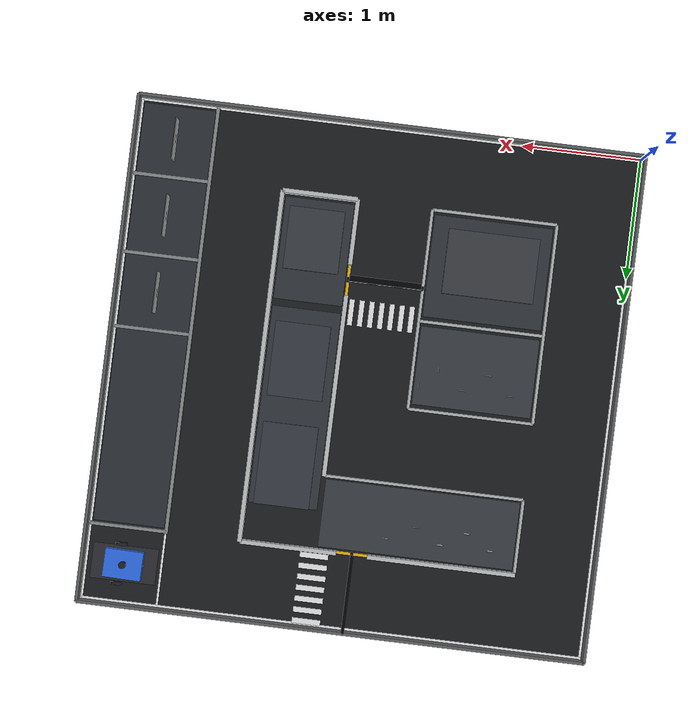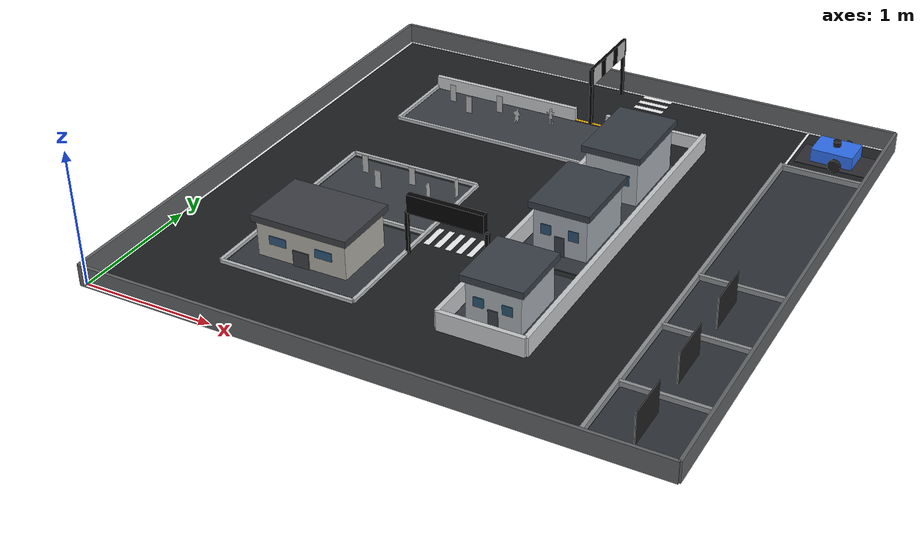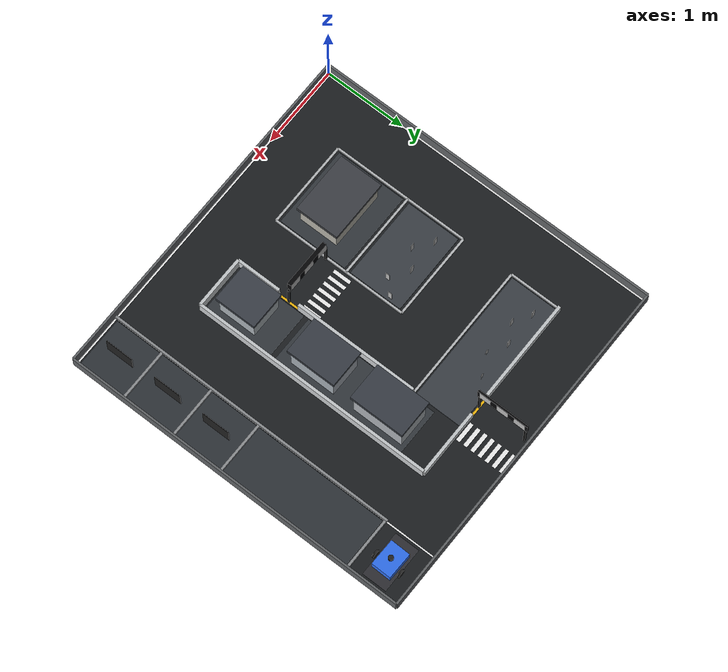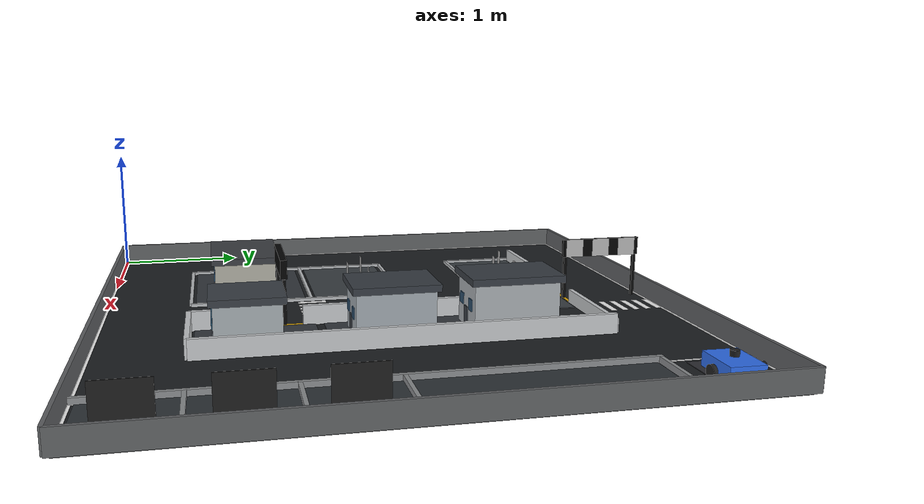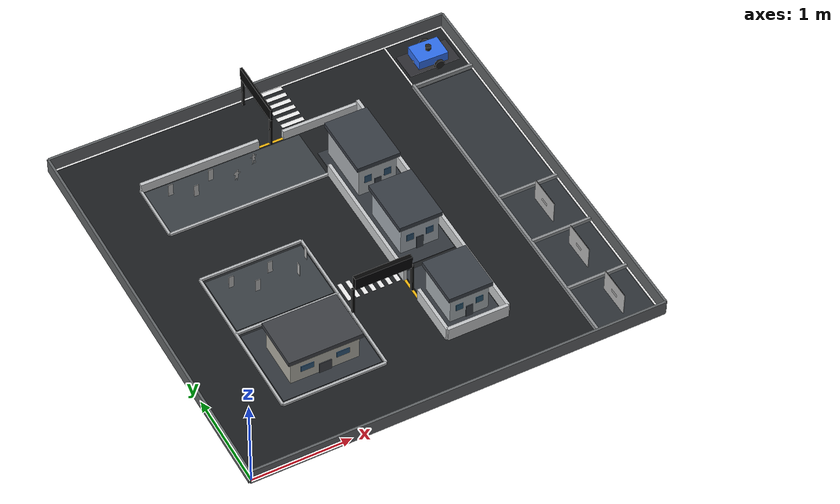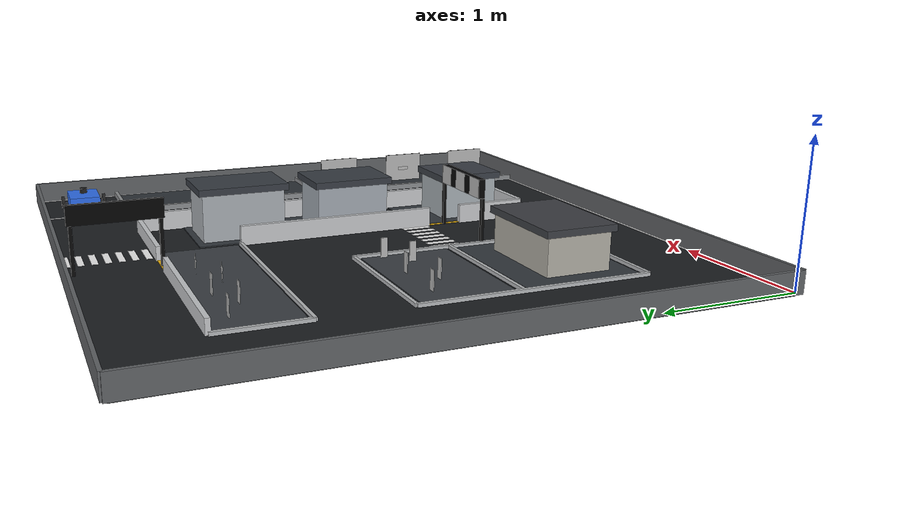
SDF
<sdf version='1.10'>
  <world name='smart_community'>
    <physics name='physics' type='ignored'>
      <max_step_size>0.002</max_step_size>
      <real_time_factor>1</real_time_factor>
      <real_time_update_rate>1000</real_time_update_rate>
    </physics>
    <plugin name='gz::sim::systems::Physics' filename='gz-sim-physics-system'/>
    <plugin name='gz::sim::systems::Sensors' filename='gz-sim-sensors-system'/>
    <plugin name='gz::sim::systems::UserCommands' filename='gz-sim-user-commands-system'/>
    <plugin name='gz::sim::systems::SceneBroadcaster' filename='gz-sim-scene-broadcaster-system'/>
    <gravity>0 0 -9.8000000000000007</gravity>
    <magnetic_field>5.5644999999999998e-06 2.2875799999999999e-05 -4.2388400000000002e-05</magnetic_field>
    <atmosphere type='adiabatic'/>
    <scene>
      <ambient>0.400000006 0.400000006 0.400000006 1</ambient>
      <background>0.699999988 0.699999988 0.699999988 1</background>
      <shadows>true</shadows>
    </scene>
    <model name='ground'>
      <static>true</static>
      <pose>2.1000000000000001 2.1000000000000001 -0.01 0 0 0</pose>
      <link name='link'>
        <collision name='collision'>
          <geometry>
            <box>
              <size>4.2000000000000002 4.2000000000000002 0.02</size>
            </box>
          </geometry>
          <surface>
            <friction>
              <ode/>
            </friction>
            <bounce/>
            <contact/>
          </surface>
        </collision>
        <visual name='visual'>
          <geometry>
            <box>
              <size>4.2000000000000002 4.2000000000000002 0.02</size>
            </box>
          </geometry>
          <material>
            <ambient>0.109999999 0.119999997 0.129999995 1</ambient>
            <diffuse>0.109999999 0.119999997 0.129999995 1</diffuse>
          </material>
        </visual>
        <pose>0 0 0 0 0 0</pose>
        <inertial>
          <pose>0 0 0 0 0 0</pose>
          <mass>1</mass>
          <inertia>
            <ixx>1</ixx>
            <ixy>0</ixy>
            <ixz>0</ixz>
            <iyy>1</iyy>
            <iyz>0</iyz>
            <izz>1</izz>
          </inertia>
        </inertial>
        <enable_wind>false</enable_wind>
      </link>
      <self_collide>false</self_collide>
    </model>
    <model name='line_outer_bottom'>
      <static>true</static>
      <pose>2.1000000000000001 0 0.0030000000000000001 0 0 0</pose>
      <link name='link'>
        <visual name='visual'>
          <geometry>
            <box>
              <size>4.2000000000000002 0.017999999999999999 0.0040000000000000001</size>
            </box>
          </geometry>
          <material>
            <ambient>0.949999988 0.949999988 0.949999988 1</ambient>
            <diffuse>0.949999988 0.949999988 0.949999988 1</diffuse>
          </material>
        </visual>
        <pose>0 0 0 0 0 0</pose>
        <inertial>
          <pose>0 0 0 0 0 0</pose>
          <mass>1</mass>
          <inertia>
            <ixx>1</ixx>
            <ixy>0</ixy>
            <ixz>0</ixz>
            <iyy>1</iyy>
            <iyz>0</iyz>
            <izz>1</izz>
          </inertia>
        </inertial>
        <enable_wind>false</enable_wind>
      </link>
      <self_collide>false</self_collide>
    </model>
    <model name='line_outer_top'>
      <static>true</static>
      <pose>2.1000000000000001 4.2000000000000002 0.0030000000000000001 0 0 0</pose>
      <link name='link'>
        <visual name='visual'>
          <geometry>
            <box>
              <size>4.2000000000000002 0.017999999999999999 0.0040000000000000001</size>
            </box>
          </geometry>
          <material>
            <ambient>0.949999988 0.949999988 0.949999988 1</ambient>
            <diffuse>0.949999988 0.949999988 0.949999988 1</diffuse>
          </material>
        </visual>
        <pose>0 0 0 0 0 0</pose>
        <inertial>
          <pose>0 0 0 0 0 0</pose>
          <mass>1</mass>
          <inertia>
            <ixx>1</ixx>
            <ixy>0</ixy>
            <ixz>0</ixz>
            <iyy>1</iyy>
            <iyz>0</iyz>
            <izz>1</izz>
          </inertia>
        </inertial>
        <enable_wind>false</enable_wind>
      </link>
      <self_collide>false</self_collide>
    </model>
    <model name='line_outer_left'>
      <static>true</static>
      <pose>0 2.1000000000000001 0.0030000000000000001 0 0 0</pose>
      <link name='link'>
        <visual name='visual'>
          <geometry>
            <box>
              <size>0.017999999999999999 4.2000000000000002 0.0040000000000000001</size>
            </box>
          </geometry>
          <material>
            <ambient>0.949999988 0.949999988 0.949999988 1</ambient>
            <diffuse>0.949999988 0.949999988 0.949999988 1</diffuse>
          </material>
        </visual>
        <pose>0 0 0 0 0 0</pose>
        <inertial>
          <pose>0 0 0 0 0 0</pose>
          <mass>1</mass>
          <inertia>
            <ixx>1</ixx>
            <ixy>0</ixy>
            <ixz>0</ixz>
            <iyy>1</iyy>
            <iyz>0</iyz>
            <izz>1</izz>
          </inertia>
        </inertial>
        <enable_wind>false</enable_wind>
      </link>
      <self_collide>false</self_collide>
    </model>
    <model name='line_outer_right'>
      <static>true</static>
      <pose>4.2000000000000002 2.1000000000000001 0.0030000000000000001 0 0 0</pose>
      <link name='link'>
        <visual name='visual'>
          <geometry>
            <box>
              <size>0.017999999999999999 4.2000000000000002 0.0040000000000000001</size>
            </box>
          </geometry>
          <material>
            <ambient>0.949999988 0.949999988 0.949999988 1</ambient>
            <diffuse>0.949999988 0.949999988 0.949999988 1</diffuse>
          </material>
        </visual>
        <pose>0 0 0 0 0 0</pose>
        <inertial>
          <pose>0 0 0 0 0 0</pose>
          <mass>1</mass>
          <inertia>
            <ixx>1</ixx>
            <ixy>0</ixy>
            <ixz>0</ixz>
            <iyy>1</iyy>
            <iyz>0</iyz>
            <izz>1</izz>
          </inertia>
        </inertial>
        <enable_wind>false</enable_wind>
      </link>
      <self_collide>false</self_collide>
    </model>
    <model name='wall_outer_bottom'>
      <static>true</static>
      <pose>2.1000000000000001 -0.025000000000000001 0.080000000000000002 0 0 0</pose>
      <link name='link'>
        <collision name='collision'>
          <geometry>
            <box>
              <size>4.25 0.025000000000000001 0.16</size>
            </box>
          </geometry>
          <surface>
            <friction>
              <ode/>
            </friction>
            <bounce/>
            <contact/>
          </surface>
        </collision>
        <visual name='visual'>
          <geometry>
            <box>
              <size>4.25 0.025000000000000001 0.16</size>
            </box>
          </geometry>
          <material>
            <ambient>0.379999995 0.389999986 0.400000006 1</ambient>
            <diffuse>0.379999995 0.389999986 0.400000006 1</diffuse>
          </material>
        </visual>
        <pose>0 0 0 0 0 0</pose>
        <inertial>
          <pose>0 0 0 0 0 0</pose>
          <mass>1</mass>
          <inertia>
            <ixx>1</ixx>
            <ixy>0</ixy>
            <ixz>0</ixz>
            <iyy>1</iyy>
            <iyz>0</iyz>
            <izz>1</izz>
          </inertia>
        </inertial>
        <enable_wind>false</enable_wind>
      </link>
      <self_collide>false</self_collide>
    </model>
    <model name='wall_outer_top'>
      <static>true</static>
      <pose>2.1000000000000001 4.2249999999999996 0.080000000000000002 0 0 0</pose>
      <link name='link'>
        <collision name='collision'>
          <geometry>
            <box>
              <size>4.25 0.025000000000000001 0.16</size>
            </box>
          </geometry>
          <surface>
            <friction>
              <ode/>
            </friction>
            <bounce/>
            <contact/>
          </surface>
        </collision>
        <visual name='visual'>
          <geometry>
            <box>
              <size>4.25 0.025000000000000001 0.16</size>
            </box>
          </geometry>
          <material>
            <ambient>0.379999995 0.389999986 0.400000006 1</ambient>
            <diffuse>0.379999995 0.389999986 0.400000006 1</diffuse>
          </material>
        </visual>
        <pose>0 0 0 0 0 0</pose>
        <inertial>
          <pose>0 0 0 0 0 0</pose>
          <mass>1</mass>
          <inertia>
            <ixx>1</ixx>
            <ixy>0</ixy>
            <ixz>0</ixz>
            <iyy>1</iyy>
            <iyz>0</iyz>
            <izz>1</izz>
          </inertia>
        </inertial>
        <enable_wind>false</enable_wind>
      </link>
      <self_collide>false</self_collide>
    </model>
    <model name='wall_outer_left'>
      <static>true</static>
      <pose>-0.025000000000000001 2.1000000000000001 0.080000000000000002 0 0 0</pose>
      <link name='link'>
        <collision name='collision'>
          <geometry>
            <box>
              <size>0.025000000000000001 4.25 0.16</size>
            </box>
          </geometry>
          <surface>
            <friction>
              <ode/>
            </friction>
            <bounce/>
            <contact/>
          </surface>
        </collision>
        <visual name='visual'>
          <geometry>
            <box>
              <size>0.025000000000000001 4.25 0.16</size>
            </box>
          </geometry>
          <material>
            <ambient>0.379999995 0.389999986 0.400000006 1</ambient>
            <diffuse>0.379999995 0.389999986 0.400000006 1</diffuse>
          </material>
        </visual>
        <pose>0 0 0 0 0 0</pose>
        <inertial>
          <pose>0 0 0 0 0 0</pose>
          <mass>1</mass>
          <inertia>
            <ixx>1</ixx>
            <ixy>0</ixy>
            <ixz>0</ixz>
            <iyy>1</iyy>
            <iyz>0</iyz>
            <izz>1</izz>
          </inertia>
        </inertial>
        <enable_wind>false</enable_wind>
      </link>
      <self_collide>false</self_collide>
    </model>
    <model name='wall_outer_right'>
      <static>true</static>
      <pose>4.2249999999999996 2.1000000000000001 0.080000000000000002 0 0 0</pose>
      <link name='link'>
        <collision name='collision'>
          <geometry>
            <box>
              <size>0.025000000000000001 4.25 0.16</size>
            </box>
          </geometry>
          <surface>
            <friction>
              <ode/>
            </friction>
            <bounce/>
            <contact/>
          </surface>
        </collision>
        <visual name='visual'>
          <geometry>
            <box>
              <size>0.025000000000000001 4.25 0.16</size>
            </box>
          </geometry>
          <material>
            <ambient>0.379999995 0.389999986 0.400000006 1</ambient>
            <diffuse>0.379999995 0.389999986 0.400000006 1</diffuse>
          </material>
        </visual>
        <pose>0 0 0 0 0 0</pose>
        <inertial>
          <pose>0 0 0 0 0 0</pose>
          <mass>1</mass>
          <inertia>
            <ixx>1</ixx>
            <ixy>0</ixy>
            <ixz>0</ixz>
            <iyy>1</iyy>
            <iyz>0</iyz>
            <izz>1</izz>
          </inertia>
        </inertial>
        <enable_wind>false</enable_wind>
      </link>
      <self_collide>false</self_collide>
    </model>
    <model name='h_top_block'>
      <static>true</static>
      <pose>1.784 3.5720000000000001 0.0030000000000000001 0 0 0</pose>
      <link name='link'>
        <visual name='visual'>
          <geometry>
            <box>
              <size>2.3119999999999998 0.017999999999999999 0.0040000000000000001</size>
            </box>
          </geometry>
          <material>
            <ambient>0.949999988 0.949999988 0.949999988 1</ambient>
            <diffuse>0.949999988 0.949999988 0.949999988 1</diffuse>
          </material>
        </visual>
        <pose>0 0 0 0 0 0</pose>
        <inertial>
          <pose>0 0 0 0 0 0</pose>
          <mass>1</mass>
          <inertia>
            <ixx>1</ixx>
            <ixy>0</ixy>
            <ixz>0</ixz>
            <iyy>1</iyy>
            <iyz>0</iyz>
            <izz>1</izz>
          </inertia>
        </inertial>
        <enable_wind>false</enable_wind>
      </link>
      <self_collide>false</self_collide>
    </model>
    <model name='h_A_lower'>
      <static>true</static>
      <pose>1.468 2.944 0.0030000000000000001 0 0 0</pose>
      <link name='link'>
        <visual name='visual'>
          <geometry>
            <box>
              <size>1.6799999999999999 0.017999999999999999 0.0040000000000000001</size>
            </box>
          </geometry>
          <material>
            <ambient>0.949999988 0.949999988 0.949999988 1</ambient>
            <diffuse>0.949999988 0.949999988 0.949999988 1</diffuse>
          </material>
        </visual>
        <pose>0 0 0 0 0 0</pose>
        <inertial>
          <pose>0 0 0 0 0 0</pose>
          <mass>1</mass>
          <inertia>
            <ixx>1</ixx>
            <ixy>0</ixy>
            <ixz>0</ixz>
            <iyy>1</iyy>
            <iyz>0</iyz>
            <izz>1</izz>
          </inertia>
        </inertial>
        <enable_wind>false</enable_wind>
      </link>
      <self_collide>false</self_collide>
    </model>
    <model name='h_B_top'>
      <static>true</static>
      <pose>1.1539999999999999 2.3039999999999998 0.0030000000000000001 0 0 0</pose>
      <link name='link'>
        <visual name='visual'>
          <geometry>
            <box>
              <size>1.052 0.017999999999999999 0.0040000000000000001</size>
            </box>
          </geometry>
          <material>
            <ambient>0.949999988 0.949999988 0.949999988 1</ambient>
            <diffuse>0.949999988 0.949999988 0.949999988 1</diffuse>
          </material>
        </visual>
        <pose>0 0 0 0 0 0</pose>
        <inertial>
          <pose>0 0 0 0 0 0</pose>
          <mass>1</mass>
          <inertia>
            <ixx>1</ixx>
            <ixy>0</ixy>
            <ixz>0</ixz>
            <iyy>1</iyy>
            <iyz>0</iyz>
            <izz>1</izz>
          </inertia>
        </inertial>
        <enable_wind>false</enable_wind>
      </link>
      <self_collide>false</self_collide>
    </model>
    <model name='h_B_split'>
      <static>true</static>
      <pose>1.1539999999999999 1.5629999999999999 0.0030000000000000001 0 0 0</pose>
      <link name='link'>
        <visual name='visual'>
          <geometry>
            <box>
              <size>1.052 0.017999999999999999 0.0040000000000000001</size>
            </box>
          </geometry>
          <material>
            <ambient>0.949999988 0.949999988 0.949999988 1</ambient>
            <diffuse>0.949999988 0.949999988 0.949999988 1</diffuse>
          </material>
        </visual>
        <pose>0 0 0 0 0 0</pose>
        <inertial>
          <pose>0 0 0 0 0 0</pose>
          <mass>1</mass>
          <inertia>
            <ixx>1</ixx>
            <ixy>0</ixy>
            <ixz>0</ixz>
            <iyy>1</iyy>
            <iyz>0</iyz>
            <izz>1</izz>
          </inertia>
        </inertial>
        <enable_wind>false</enable_wind>
      </link>
      <self_collide>false</self_collide>
    </model>
    <model name='h_B_bottom'>
      <static>true</static>
      <pose>1.1539999999999999 0.624 0.0030000000000000001 0 0 0</pose>
      <link name='link'>
        <visual name='visual'>
          <geometry>
            <box>
              <size>1.052 0.017999999999999999 0.0040000000000000001</size>
            </box>
          </geometry>
          <material>
            <ambient>0.949999988 0.949999988 0.949999988 1</ambient>
            <diffuse>0.949999988 0.949999988 0.949999988 1</diffuse>
          </material>
        </visual>
        <pose>0 0 0 0 0 0</pose>
        <inertial>
          <pose>0 0 0 0 0 0</pose>
          <mass>1</mass>
          <inertia>
            <ixx>1</ixx>
            <ixy>0</ixy>
            <ixz>0</ixz>
            <iyy>1</iyy>
            <iyz>0</iyz>
            <izz>1</izz>
          </inertia>
        </inertial>
        <enable_wind>false</enable_wind>
      </link>
      <self_collide>false</self_collide>
    </model>
    <model name='h_center_bottom'>
      <static>true</static>
      <pose>2.6240000000000001 0.624 0.0030000000000000001 0 0 0</pose>
      <link name='link'>
        <visual name='visual'>
          <geometry>
            <box>
              <size>0.63200000000000001 0.017999999999999999 0.0040000000000000001</size>
            </box>
          </geometry>
          <material>
            <ambient>0.949999988 0.949999988 0.949999988 1</ambient>
            <diffuse>0.949999988 0.949999988 0.949999988 1</diffuse>
          </material>
        </visual>
        <pose>0 0 0 0 0 0</pose>
        <inertial>
          <pose>0 0 0 0 0 0</pose>
          <mass>1</mass>
          <inertia>
            <ixx>1</ixx>
            <ixy>0</ixy>
            <ixz>0</ixz>
            <iyy>1</iyy>
            <iyz>0</iyz>
            <izz>1</izz>
          </inertia>
        </inertial>
        <enable_wind>false</enable_wind>
      </link>
      <self_collide>false</self_collide>
    </model>
    <model name='h_parking_top'>
      <static>true</static>
      <pose>3.8839999999999999 3.5720000000000001 0.0030000000000000001 0 0 0</pose>
      <link name='link'>
        <visual name='visual'>
          <geometry>
            <box>
              <size>0.63200000000000001 0.017999999999999999 0.0040000000000000001</size>
            </box>
          </geometry>
          <material>
            <ambient>0.949999988 0.949999988 0.949999988 1</ambient>
            <diffuse>0.949999988 0.949999988 0.949999988 1</diffuse>
          </material>
        </visual>
        <pose>0 0 0 0 0 0</pose>
        <inertial>
          <pose>0 0 0 0 0 0</pose>
          <mass>1</mass>
          <inertia>
            <ixx>1</ixx>
            <ixy>0</ixy>
            <ixz>0</ixz>
            <iyy>1</iyy>
            <iyz>0</iyz>
            <izz>1</izz>
          </inertia>
        </inertial>
        <enable_wind>false</enable_wind>
      </link>
      <self_collide>false</self_collide>
    </model>
    <model name='h_parking_3top'>
      <static>true</static>
      <pose>3.8839999999999999 1.9119999999999999 0.0030000000000000001 0 0 0</pose>
      <link name='link'>
        <visual name='visual'>
          <geometry>
            <box>
              <size>0.63200000000000001 0.017999999999999999 0.0040000000000000001</size>
            </box>
          </geometry>
          <material>
            <ambient>0.949999988 0.949999988 0.949999988 1</ambient>
            <diffuse>0.949999988 0.949999988 0.949999988 1</diffuse>
          </material>
        </visual>
        <pose>0 0 0 0 0 0</pose>
        <inertial>
          <pose>0 0 0 0 0 0</pose>
          <mass>1</mass>
          <inertia>
            <ixx>1</ixx>
            <ixy>0</ixy>
            <ixz>0</ixz>
            <iyy>1</iyy>
            <iyz>0</iyz>
            <izz>1</izz>
          </inertia>
        </inertial>
        <enable_wind>false</enable_wind>
      </link>
      <self_collide>false</self_collide>
    </model>
    <model name='h_parking_2top'>
      <static>true</static>
      <pose>3.8839999999999999 1.2849999999999999 0.0030000000000000001 0 0 0</pose>
      <link name='link'>
        <visual name='visual'>
          <geometry>
            <box>
              <size>0.63200000000000001 0.017999999999999999 0.0040000000000000001</size>
            </box>
          </geometry>
          <material>
            <ambient>0.949999988 0.949999988 0.949999988 1</ambient>
            <diffuse>0.949999988 0.949999988 0.949999988 1</diffuse>
          </material>
        </visual>
        <pose>0 0 0 0 0 0</pose>
        <inertial>
          <pose>0 0 0 0 0 0</pose>
          <mass>1</mass>
          <inertia>
            <ixx>1</ixx>
            <ixy>0</ixy>
            <ixz>0</ixz>
            <iyy>1</iyy>
            <iyz>0</iyz>
            <izz>1</izz>
          </inertia>
        </inertial>
        <enable_wind>false</enable_wind>
      </link>
      <self_collide>false</self_collide>
    </model>
    <model name='h_parking_1top'>
      <static>true</static>
      <pose>3.8839999999999999 0.624 0.0030000000000000001 0 0 0</pose>
      <link name='link'>
        <visual name='visual'>
          <geometry>
            <box>
              <size>0.63200000000000001 0.017999999999999999 0.0040000000000000001</size>
            </box>
          </geometry>
          <material>
            <ambient>0.949999988 0.949999988 0.949999988 1</ambient>
            <diffuse>0.949999988 0.949999988 0.949999988 1</diffuse>
          </material>
        </visual>
        <pose>0 0 0 0 0 0</pose>
        <inertial>
          <pose>0 0 0 0 0 0</pose>
          <mass>1</mass>
          <inertia>
            <ixx>1</ixx>
            <ixy>0</ixy>
            <ixz>0</ixz>
            <iyy>1</iyy>
            <iyz>0</iyz>
            <izz>1</izz>
          </inertia>
        </inertial>
        <enable_wind>false</enable_wind>
      </link>
      <self_collide>false</self_collide>
    </model>
    <model name='v_A_left'>
      <static>true</static>
      <pose>0.628 3.258 0.0030000000000000001 0 0 0</pose>
      <link name='link'>
        <visual name='visual'>
          <geometry>
            <box>
              <size>0.017999999999999999 0.628 0.0040000000000000001</size>
            </box>
          </geometry>
          <material>
            <ambient>0.949999988 0.949999988 0.949999988 1</ambient>
            <diffuse>0.949999988 0.949999988 0.949999988 1</diffuse>
          </material>
        </visual>
        <pose>0 0 0 0 0 0</pose>
        <inertial>
          <pose>0 0 0 0 0 0</pose>
          <mass>1</mass>
          <inertia>
            <ixx>1</ixx>
            <ixy>0</ixy>
            <ixz>0</ixz>
            <iyy>1</iyy>
            <iyz>0</iyz>
            <izz>1</izz>
          </inertia>
        </inertial>
        <enable_wind>false</enable_wind>
      </link>
      <self_collide>false</self_collide>
    </model>
    <model name='v_B_left'>
      <static>true</static>
      <pose>0.628 1.464 0.0030000000000000001 0 0 0</pose>
      <link name='link'>
        <visual name='visual'>
          <geometry>
            <box>
              <size>0.017999999999999999 1.6799999999999999 0.0040000000000000001</size>
            </box>
          </geometry>
          <material>
            <ambient>0.949999988 0.949999988 0.949999988 1</ambient>
            <diffuse>0.949999988 0.949999988 0.949999988 1</diffuse>
          </material>
        </visual>
        <pose>0 0 0 0 0 0</pose>
        <inertial>
          <pose>0 0 0 0 0 0</pose>
          <mass>1</mass>
          <inertia>
            <ixx>1</ixx>
            <ixy>0</ixy>
            <ixz>0</ixz>
            <iyy>1</iyy>
            <iyz>0</iyz>
            <izz>1</izz>
          </inertia>
        </inertial>
        <enable_wind>false</enable_wind>
      </link>
      <self_collide>false</self_collide>
    </model>
    <model name='v_B_right'>
      <static>true</static>
      <pose>1.6799999999999999 1.464 0.0030000000000000001 0 0 0</pose>
      <link name='link'>
        <visual name='visual'>
          <geometry>
            <box>
              <size>0.017999999999999999 1.6799999999999999 0.0040000000000000001</size>
            </box>
          </geometry>
          <material>
            <ambient>0.949999988 0.949999988 0.949999988 1</ambient>
            <diffuse>0.949999988 0.949999988 0.949999988 1</diffuse>
          </material>
        </visual>
        <pose>0 0 0 0 0 0</pose>
        <inertial>
          <pose>0 0 0 0 0 0</pose>
          <mass>1</mass>
          <inertia>
            <ixx>1</ixx>
            <ixy>0</ixy>
            <ixz>0</ixz>
            <iyy>1</iyy>
            <iyz>0</iyz>
            <izz>1</izz>
          </inertia>
        </inertial>
        <enable_wind>false</enable_wind>
      </link>
      <self_collide>false</self_collide>
    </model>
    <model name='v_center_left'>
      <static>true</static>
      <pose>2.3079999999999998 1.784 0.0030000000000000001 0 0 0</pose>
      <link name='link'>
        <visual name='visual'>
          <geometry>
            <box>
              <size>0.017999999999999999 2.3199999999999998 0.0040000000000000001</size>
            </box>
          </geometry>
          <material>
            <ambient>0.949999988 0.949999988 0.949999988 1</ambient>
            <diffuse>0.949999988 0.949999988 0.949999988 1</diffuse>
          </material>
        </visual>
        <pose>0 0 0 0 0 0</pose>
        <inertial>
          <pose>0 0 0 0 0 0</pose>
          <mass>1</mass>
          <inertia>
            <ixx>1</ixx>
            <ixy>0</ixy>
            <ixz>0</ixz>
            <iyy>1</iyy>
            <iyz>0</iyz>
            <izz>1</izz>
          </inertia>
        </inertial>
        <enable_wind>false</enable_wind>
      </link>
      <self_collide>false</self_collide>
    </model>
    <model name='v_center_right'>
      <static>true</static>
      <pose>2.9399999999999999 2.0979999999999999 0.0030000000000000001 0 0 0</pose>
      <link name='link'>
        <visual name='visual'>
          <geometry>
            <box>
              <size>0.017999999999999999 2.948 0.0040000000000000001</size>
            </box>
          </geometry>
          <material>
            <ambient>0.949999988 0.949999988 0.949999988 1</ambient>
            <diffuse>0.949999988 0.949999988 0.949999988 1</diffuse>
          </material>
        </visual>
        <pose>0 0 0 0 0 0</pose>
        <inertial>
          <pose>0 0 0 0 0 0</pose>
          <mass>1</mass>
          <inertia>
            <ixx>1</ixx>
            <ixy>0</ixy>
            <ixz>0</ixz>
            <iyy>1</iyy>
            <iyz>0</iyz>
            <izz>1</izz>
          </inertia>
        </inertial>
        <enable_wind>false</enable_wind>
      </link>
      <self_collide>false</self_collide>
    </model>
    <model name='v_parking_left'>
      <static>true</static>
      <pose>3.5680000000000001 2.1000000000000001 0.0030000000000000001 0 0 0</pose>
      <link name='link'>
        <visual name='visual'>
          <geometry>
            <box>
              <size>0.017999999999999999 4.2000000000000002 0.0040000000000000001</size>
            </box>
          </geometry>
          <material>
            <ambient>0.949999988 0.949999988 0.949999988 1</ambient>
            <diffuse>0.949999988 0.949999988 0.949999988 1</diffuse>
          </material>
        </visual>
        <pose>0 0 0 0 0 0</pose>
        <inertial>
          <pose>0 0 0 0 0 0</pose>
          <mass>1</mass>
          <inertia>
            <ixx>1</ixx>
            <ixy>0</ixy>
            <ixz>0</ixz>
            <iyy>1</iyy>
            <iyz>0</iyz>
            <izz>1</izz>
          </inertia>
        </inertial>
        <enable_wind>false</enable_wind>
      </link>
      <self_collide>false</self_collide>
    </model>
    <model name='crosswalk_top_0'>
      <static>true</static>
      <pose>2.3100000000000001 3.6231 0.0040000000000000001 0 0 0</pose>
      <link name='link'>
        <visual name='visual'>
          <geometry>
            <box>
              <size>0.23999999999999999 0.046199999999999998 0.0040000000000000001</size>
            </box>
          </geometry>
          <material>
            <ambient>0.949999988 0.949999988 0.949999988 1</ambient>
            <diffuse>0.949999988 0.949999988 0.949999988 1</diffuse>
          </material>
        </visual>
        <pose>0 0 0 0 0 0</pose>
        <inertial>
          <pose>0 0 0 0 0 0</pose>
          <mass>1</mass>
          <inertia>
            <ixx>1</ixx>
            <ixy>0</ixy>
            <ixz>0</ixz>
            <iyy>1</iyy>
            <iyz>0</iyz>
            <izz>1</izz>
          </inertia>
        </inertial>
        <enable_wind>false</enable_wind>
      </link>
      <self_collide>false</self_collide>
    </model>
    <model name='crosswalk_top_1'>
      <static>true</static>
      <pose>2.3100000000000001 3.7153999999999998 0.0040000000000000001 0 0 0</pose>
      <link name='link'>
        <visual name='visual'>
          <geometry>
            <box>
              <size>0.23999999999999999 0.046199999999999998 0.0040000000000000001</size>
            </box>
          </geometry>
          <material>
            <ambient>0.949999988 0.949999988 0.949999988 1</ambient>
            <diffuse>0.949999988 0.949999988 0.949999988 1</diffuse>
          </material>
        </visual>
        <pose>0 0 0 0 0 0</pose>
        <inertial>
          <pose>0 0 0 0 0 0</pose>
          <mass>1</mass>
          <inertia>
            <ixx>1</ixx>
            <ixy>0</ixy>
            <ixz>0</ixz>
            <iyy>1</iyy>
            <iyz>0</iyz>
            <izz>1</izz>
          </inertia>
        </inertial>
        <enable_wind>false</enable_wind>
      </link>
      <self_collide>false</self_collide>
    </model>
    <model name='crosswalk_top_2'>
      <static>true</static>
      <pose>2.3100000000000001 3.8077000000000001 0.0040000000000000001 0 0 0</pose>
      <link name='link'>
        <visual name='visual'>
          <geometry>
            <box>
              <size>0.23999999999999999 0.046199999999999998 0.0040000000000000001</size>
            </box>
          </geometry>
          <material>
            <ambient>0.949999988 0.949999988 0.949999988 1</ambient>
            <diffuse>0.949999988 0.949999988 0.949999988 1</diffuse>
          </material>
        </visual>
        <pose>0 0 0 0 0 0</pose>
        <inertial>
          <pose>0 0 0 0 0 0</pose>
          <mass>1</mass>
          <inertia>
            <ixx>1</ixx>
            <ixy>0</ixy>
            <ixz>0</ixz>
            <iyy>1</iyy>
            <iyz>0</iyz>
            <izz>1</izz>
          </inertia>
        </inertial>
        <enable_wind>false</enable_wind>
      </link>
      <self_collide>false</self_collide>
    </model>
    <model name='crosswalk_top_3'>
      <static>true</static>
      <pose>2.3100000000000001 3.8999999999999999 0.0040000000000000001 0 0 0</pose>
      <link name='link'>
        <visual name='visual'>
          <geometry>
            <box>
              <size>0.23999999999999999 0.046199999999999998 0.0040000000000000001</size>
            </box>
          </geometry>
          <material>
            <ambient>0.949999988 0.949999988 0.949999988 1</ambient>
            <diffuse>0.949999988 0.949999988 0.949999988 1</diffuse>
          </material>
        </visual>
        <pose>0 0 0 0 0 0</pose>
        <inertial>
          <pose>0 0 0 0 0 0</pose>
          <mass>1</mass>
          <inertia>
            <ixx>1</ixx>
            <ixy>0</ixy>
            <ixz>0</ixz>
            <iyy>1</iyy>
            <iyz>0</iyz>
            <izz>1</izz>
          </inertia>
        </inertial>
        <enable_wind>false</enable_wind>
      </link>
      <self_collide>false</self_collide>
    </model>
    <model name='crosswalk_top_4'>
      <static>true</static>
      <pose>2.3100000000000001 3.9923000000000002 0.0040000000000000001 0 0 0</pose>
      <link name='link'>
        <visual name='visual'>
          <geometry>
            <box>
              <size>0.23999999999999999 0.046199999999999998 0.0040000000000000001</size>
            </box>
          </geometry>
          <material>
            <ambient>0.949999988 0.949999988 0.949999988 1</ambient>
            <diffuse>0.949999988 0.949999988 0.949999988 1</diffuse>
          </material>
        </visual>
        <pose>0 0 0 0 0 0</pose>
        <inertial>
          <pose>0 0 0 0 0 0</pose>
          <mass>1</mass>
          <inertia>
            <ixx>1</ixx>
            <ixy>0</ixy>
            <ixz>0</ixz>
            <iyy>1</iyy>
            <iyz>0</iyz>
            <izz>1</izz>
          </inertia>
        </inertial>
        <enable_wind>false</enable_wind>
      </link>
      <self_collide>false</self_collide>
    </model>
    <model name='crosswalk_top_5'>
      <static>true</static>
      <pose>2.3100000000000001 4.0846 0.0040000000000000001 0 0 0</pose>
      <link name='link'>
        <visual name='visual'>
          <geometry>
            <box>
              <size>0.23999999999999999 0.046199999999999998 0.0040000000000000001</size>
            </box>
          </geometry>
          <material>
            <ambient>0.949999988 0.949999988 0.949999988 1</ambient>
            <diffuse>0.949999988 0.949999988 0.949999988 1</diffuse>
          </material>
        </visual>
        <pose>0 0 0 0 0 0</pose>
        <inertial>
          <pose>0 0 0 0 0 0</pose>
          <mass>1</mass>
          <inertia>
            <ixx>1</ixx>
            <ixy>0</ixy>
            <ixz>0</ixz>
            <iyy>1</iyy>
            <iyz>0</iyz>
            <izz>1</izz>
          </inertia>
        </inertial>
        <enable_wind>false</enable_wind>
      </link>
      <self_collide>false</self_collide>
    </model>
    <model name='crosswalk_top_6'>
      <static>true</static>
      <pose>2.3100000000000001 4.1768999999999998 0.0040000000000000001 0 0 0</pose>
      <link name='link'>
        <visual name='visual'>
          <geometry>
            <box>
              <size>0.23999999999999999 0.046199999999999998 0.0040000000000000001</size>
            </box>
          </geometry>
          <material>
            <ambient>0.949999988 0.949999988 0.949999988 1</ambient>
            <diffuse>0.949999988 0.949999988 0.949999988 1</diffuse>
          </material>
        </visual>
        <pose>0 0 0 0 0 0</pose>
        <inertial>
          <pose>0 0 0 0 0 0</pose>
          <mass>1</mass>
          <inertia>
            <ixx>1</ixx>
            <ixy>0</ixy>
            <ixz>0</ixz>
            <iyy>1</iyy>
            <iyz>0</iyz>
            <izz>1</izz>
          </inertia>
        </inertial>
        <enable_wind>false</enable_wind>
      </link>
      <self_collide>false</self_collide>
    </model>
    <model name='crosswalk_mid_0'>
      <static>true</static>
      <pose>1.7462 1.5600000000000001 0.0040000000000000001 0 0 0</pose>
      <link name='link'>
        <visual name='visual'>
          <geometry>
            <box>
              <size>0.042299999999999997 0.22 0.0040000000000000001</size>
            </box>
          </geometry>
          <material>
            <ambient>0.949999988 0.949999988 0.949999988 1</ambient>
            <diffuse>0.949999988 0.949999988 0.949999988 1</diffuse>
          </material>
        </visual>
        <pose>0 0 0 0 0 0</pose>
        <inertial>
          <pose>0 0 0 0 0 0</pose>
          <mass>1</mass>
          <inertia>
            <ixx>1</ixx>
            <ixy>0</ixy>
            <ixz>0</ixz>
            <iyy>1</iyy>
            <iyz>0</iyz>
            <izz>1</izz>
          </inertia>
        </inertial>
        <enable_wind>false</enable_wind>
      </link>
      <self_collide>false</self_collide>
    </model>
    <model name='crosswalk_mid_1'>
      <static>true</static>
      <pose>1.8308 1.5600000000000001 0.0040000000000000001 0 0 0</pose>
      <link name='link'>
        <visual name='visual'>
          <geometry>
            <box>
              <size>0.042299999999999997 0.22 0.0040000000000000001</size>
            </box>
          </geometry>
          <material>
            <ambient>0.949999988 0.949999988 0.949999988 1</ambient>
            <diffuse>0.949999988 0.949999988 0.949999988 1</diffuse>
          </material>
        </visual>
        <pose>0 0 0 0 0 0</pose>
        <inertial>
          <pose>0 0 0 0 0 0</pose>
          <mass>1</mass>
          <inertia>
            <ixx>1</ixx>
            <ixy>0</ixy>
            <ixz>0</ixz>
            <iyy>1</iyy>
            <iyz>0</iyz>
            <izz>1</izz>
          </inertia>
        </inertial>
        <enable_wind>false</enable_wind>
      </link>
      <self_collide>false</self_collide>
    </model>
    <model name='crosswalk_mid_2'>
      <static>true</static>
      <pose>1.9154 1.5600000000000001 0.0040000000000000001 0 0 0</pose>
      <link name='link'>
        <visual name='visual'>
          <geometry>
            <box>
              <size>0.042299999999999997 0.22 0.0040000000000000001</size>
            </box>
          </geometry>
          <material>
            <ambient>0.949999988 0.949999988 0.949999988 1</ambient>
            <diffuse>0.949999988 0.949999988 0.949999988 1</diffuse>
          </material>
        </visual>
        <pose>0 0 0 0 0 0</pose>
        <inertial>
          <pose>0 0 0 0 0 0</pose>
          <mass>1</mass>
          <inertia>
            <ixx>1</ixx>
            <ixy>0</ixy>
            <ixz>0</ixz>
            <iyy>1</iyy>
            <iyz>0</iyz>
            <izz>1</izz>
          </inertia>
        </inertial>
        <enable_wind>false</enable_wind>
      </link>
      <self_collide>false</self_collide>
    </model>
    <model name='crosswalk_mid_3'>
      <static>true</static>
      <pose>2 1.5600000000000001 0.0040000000000000001 0 0 0</pose>
      <link name='link'>
        <visual name='visual'>
          <geometry>
            <box>
              <size>0.042299999999999997 0.22 0.0040000000000000001</size>
            </box>
          </geometry>
          <material>
            <ambient>0.949999988 0.949999988 0.949999988 1</ambient>
            <diffuse>0.949999988 0.949999988 0.949999988 1</diffuse>
          </material>
        </visual>
        <pose>0 0 0 0 0 0</pose>
        <inertial>
          <pose>0 0 0 0 0 0</pose>
          <mass>1</mass>
          <inertia>
            <ixx>1</ixx>
            <ixy>0</ixy>
            <ixz>0</ixz>
            <iyy>1</iyy>
            <iyz>0</iyz>
            <izz>1</izz>
          </inertia>
        </inertial>
        <enable_wind>false</enable_wind>
      </link>
      <self_collide>false</self_collide>
    </model>
    <model name='crosswalk_mid_4'>
      <static>true</static>
      <pose>2.0846 1.5600000000000001 0.0040000000000000001 0 0 0</pose>
      <link name='link'>
        <visual name='visual'>
          <geometry>
            <box>
              <size>0.042299999999999997 0.22 0.0040000000000000001</size>
            </box>
          </geometry>
          <material>
            <ambient>0.949999988 0.949999988 0.949999988 1</ambient>
            <diffuse>0.949999988 0.949999988 0.949999988 1</diffuse>
          </material>
        </visual>
        <pose>0 0 0 0 0 0</pose>
        <inertial>
          <pose>0 0 0 0 0 0</pose>
          <mass>1</mass>
          <inertia>
            <ixx>1</ixx>
            <ixy>0</ixy>
            <ixz>0</ixz>
            <iyy>1</iyy>
            <iyz>0</iyz>
            <izz>1</izz>
          </inertia>
        </inertial>
        <enable_wind>false</enable_wind>
      </link>
      <self_collide>false</self_collide>
    </model>
    <model name='crosswalk_mid_5'>
      <static>true</static>
      <pose>2.1692 1.5600000000000001 0.0040000000000000001 0 0 0</pose>
      <link name='link'>
        <visual name='visual'>
          <geometry>
            <box>
              <size>0.042299999999999997 0.22 0.0040000000000000001</size>
            </box>
          </geometry>
          <material>
            <ambient>0.949999988 0.949999988 0.949999988 1</ambient>
            <diffuse>0.949999988 0.949999988 0.949999988 1</diffuse>
          </material>
        </visual>
        <pose>0 0 0 0 0 0</pose>
        <inertial>
          <pose>0 0 0 0 0 0</pose>
          <mass>1</mass>
          <inertia>
            <ixx>1</ixx>
            <ixy>0</ixy>
            <ixz>0</ixz>
            <iyy>1</iyy>
            <iyz>0</iyz>
            <izz>1</izz>
          </inertia>
        </inertial>
        <enable_wind>false</enable_wind>
      </link>
      <self_collide>false</self_collide>
    </model>
    <model name='crosswalk_mid_6'>
      <static>true</static>
      <pose>2.2538 1.5600000000000001 0.0040000000000000001 0 0 0</pose>
      <link name='link'>
        <visual name='visual'>
          <geometry>
            <box>
              <size>0.042299999999999997 0.22 0.0040000000000000001</size>
            </box>
          </geometry>
          <material>
            <ambient>0.949999988 0.949999988 0.949999988 1</ambient>
            <diffuse>0.949999988 0.949999988 0.949999988 1</diffuse>
          </material>
        </visual>
        <pose>0 0 0 0 0 0</pose>
        <inertial>
          <pose>0 0 0 0 0 0</pose>
          <mass>1</mass>
          <inertia>
            <ixx>1</ixx>
            <ixy>0</ixy>
            <ixz>0</ixz>
            <iyy>1</iyy>
            <iyz>0</iyz>
            <izz>1</izz>
          </inertia>
        </inertial>
        <enable_wind>false</enable_wind>
      </link>
      <self_collide>false</self_collide>
    </model>
    <model name='stopline_top'>
      <static>true</static>
      <pose>2.02 3.5699999999999998 0.0040000000000000001 0 0 0</pose>
      <link name='link'>
        <visual name='visual'>
          <geometry>
            <box>
              <size>0.38 0.025000000000000001 0.0040000000000000001</size>
            </box>
          </geometry>
          <material>
            <ambient>0.949999988 0.720000029 0.0500000007 1</ambient>
            <diffuse>0.949999988 0.720000029 0.0500000007 1</diffuse>
          </material>
        </visual>
        <pose>0 0 0 0 0 0</pose>
        <inertial>
          <pose>0 0 0 0 0 0</pose>
          <mass>1</mass>
          <inertia>
            <ixx>1</ixx>
            <ixy>0</ixy>
            <ixz>0</ixz>
            <iyy>1</iyy>
            <iyz>0</iyz>
            <izz>1</izz>
          </inertia>
        </inertial>
        <enable_wind>false</enable_wind>
      </link>
      <self_collide>false</self_collide>
    </model>
    <model name='stopline_mid'>
      <static>true</static>
      <pose>2.3100000000000001 1.3400000000000001 0.0040000000000000001 0 0 0</pose>
      <link name='link'>
        <visual name='visual'>
          <geometry>
            <box>
              <size>0.025000000000000001 0.35999999999999999 0.0040000000000000001</size>
            </box>
          </geometry>
          <material>
            <ambient>0.949999988 0.720000029 0.0500000007 1</ambient>
            <diffuse>0.949999988 0.720000029 0.0500000007 1</diffuse>
          </material>
        </visual>
        <pose>0 0 0 0 0 0</pose>
        <inertial>
          <pose>0 0 0 0 0 0</pose>
          <mass>1</mass>
          <inertia>
            <ixx>1</ixx>
            <ixy>0</ixy>
            <ixz>0</ixz>
            <iyy>1</iyy>
            <iyz>0</iyz>
            <izz>1</izz>
          </inertia>
        </inertial>
        <enable_wind>false</enable_wind>
      </link>
      <self_collide>false</self_collide>
    </model>
    <include>
      <uri>file:///home/biao/aic_ws/install/smart_community_gazebo/share/smart_community_gazebo/models/vehicle_3</uri>
      <name>vehicle_3_board</name>
      <pose>3.8799999999999999 1.5980000000000001 0 0 0 0</pose>
    </include>
    <include>
      <uri>file:///home/biao/aic_ws/install/smart_community_gazebo/share/smart_community_gazebo/models/vehicle_2</uri>
      <name>vehicle_2_board</name>
      <pose>3.8799999999999999 0.95599999999999996 0 0 0 0</pose>
    </include>
    <include>
      <uri>file:///home/biao/aic_ws/install/smart_community_gazebo/share/smart_community_gazebo/models/vehicle_1</uri>
      <name>vehicle_1_board</name>
      <pose>3.8799999999999999 0.314 0 0 0 0</pose>
    </include>
    <model name='start_finish_zone'>
      <static>true</static>
      <pose>3.8799999999999999 3.8799999999999999 0.0030000000000000001 0 0 0</pose>
      <link name='link'>
        <visual name='visual'>
          <geometry>
            <box>
              <size>0.55000000000000004 0.29999999999999999 0.0040000000000000001</size>
            </box>
          </geometry>
          <material>
            <ambient>0.180000007 0.180000007 0.200000003 1</ambient>
            <diffuse>0.180000007 0.180000007 0.200000003 1</diffuse>
          </material>
        </visual>
        <pose>0 0 0 0 0 0</pose>
        <inertial>
          <pose>0 0 0 0 0 0</pose>
          <mass>1</mass>
          <inertia>
            <ixx>1</ixx>
            <ixy>0</ixy>
            <ixz>0</ixz>
            <iyy>1</iyy>
            <iyz>0</iyz>
            <izz>1</izz>
          </inertia>
        </inertial>
        <enable_wind>false</enable_wind>
      </link>
      <self_collide>false</self_collide>
    </model>
    <include>
      <uri>file:///home/biao/aic_ws/install/smart_community_gazebo/share/smart_community_gazebo/models/community_person_01</uri>
      <name>A_person_1</name>
      <pose>0.85999999999999999 3.3999999999999999 0 0 0 1.5707959999999999</pose>
    </include>
    <include>
      <uri>file:///home/biao/aic_ws/install/smart_community_gazebo/share/smart_community_gazebo/models/community_person_02</uri>
      <name>A_person_2</name>
      <pose>1.0700000000000001 3.2799999999999998 0 0 0 1.5707959999999999</pose>
    </include>
    <include>
      <uri>file:///home/biao/aic_ws/install/smart_community_gazebo/share/smart_community_gazebo/models/noncommunity_person_F1</uri>
      <name>A_person_3</name>
      <pose>1.28 3.3999999999999999 0 0 0 1.5707959999999999</pose>
    </include>
    <include>
      <uri>file:///home/biao/aic_ws/install/smart_community_gazebo/share/smart_community_gazebo/models/community_person_03</uri>
      <name>A_person_4</name>
      <pose>1.5 3.2799999999999998 0 0 0 1.5707959999999999</pose>
    </include>
    <include>
      <uri>file:///home/biao/aic_ws/install/smart_community_gazebo/share/smart_community_gazebo/models/community_person_04</uri>
      <name>A_person_5</name>
      <pose>1.73 3.3999999999999999 0 0 0 1.5707959999999999</pose>
    </include>
    <include>
      <uri>file:///home/biao/aic_ws/install/smart_community_gazebo/share/smart_community_gazebo/models/community_person_05</uri>
      <name>B_person_1</name>
      <pose>0.84999999999999998 2.1000000000000001 0 0 0 1.5707959999999999</pose>
    </include>
    <include>
      <uri>file:///home/biao/aic_ws/install/smart_community_gazebo/share/smart_community_gazebo/models/community_person_06</uri>
      <name>B_person_2</name>
      <pose>1.05 1.95 0 0 0 1.5707959999999999</pose>
    </include>
    <include>
      <uri>file:///home/biao/aic_ws/install/smart_community_gazebo/share/smart_community_gazebo/models/noncommunity_person_F2</uri>
      <name>B_person_3</name>
      <pose>1.25 2.1000000000000001 0 0 0 1.5707959999999999</pose>
    </include>
    <include>
      <uri>file:///home/biao/aic_ws/install/smart_community_gazebo/share/smart_community_gazebo/models/community_person_07</uri>
      <name>B_person_4</name>
      <pose>1.47 1.95 0 0 0 0</pose>
    </include>
    <include>
      <uri>file:///home/biao/aic_ws/install/smart_community_gazebo/share/smart_community_gazebo/models/community_person_08</uri>
      <name>B_person_5</name>
      <pose>1.6200000000000001 2.1000000000000001 0 0 0 0</pose>
    </include>
    <model name='plaza_A'>
      <static>true</static>
      <pose>1.47 3.2549999999999999 0.0040000000000000001 0 0 0</pose>
      <link name='link'>
        <visual name='visual'>
          <geometry>
            <box>
              <size>1.6399999999999999 0.56999999999999995 0.0080000000000000002</size>
            </box>
          </geometry>
          <material>
            <ambient>0.230000004 0.25 0.270000011 1</ambient>
            <diffuse>0.230000004 0.25 0.270000011 1</diffuse>
          </material>
        </visual>
        <pose>0 0 0 0 0 0</pose>
        <inertial>
          <pose>0 0 0 0 0 0</pose>
          <mass>1</mass>
          <inertia>
            <ixx>1</ixx>
            <ixy>0</ixy>
            <ixz>0</ixz>
            <iyy>1</iyy>
            <iyz>0</iyz>
            <izz>1</izz>
          </inertia>
        </inertial>
        <enable_wind>false</enable_wind>
      </link>
      <self_collide>false</self_collide>
    </model>
    <model name='plaza_B_people'>
      <static>true</static>
      <pose>1.155 1.9299999999999999 0.0040000000000000001 0 0 0</pose>
      <link name='link'>
        <visual name='visual'>
          <geometry>
            <box>
              <size>1 0.66000000000000003 0.0080000000000000002</size>
            </box>
          </geometry>
          <material>
            <ambient>0.230000004 0.25 0.270000011 1</ambient>
            <diffuse>0.230000004 0.25 0.270000011 1</diffuse>
          </material>
        </visual>
        <pose>0 0 0 0 0 0</pose>
        <inertial>
          <pose>0 0 0 0 0 0</pose>
          <mass>1</mass>
          <inertia>
            <ixx>1</ixx>
            <ixy>0</ixy>
            <ixz>0</ixz>
            <iyy>1</iyy>
            <iyz>0</iyz>
            <izz>1</izz>
          </inertia>
        </inertial>
        <enable_wind>false</enable_wind>
      </link>
      <self_collide>false</self_collide>
    </model>
    <model name='plaza_B_lower'>
      <static>true</static>
      <pose>1.155 1.0900000000000001 0.0040000000000000001 0 0 0</pose>
      <link name='link'>
        <visual name='visual'>
          <geometry>
            <box>
              <size>1 0.85999999999999999 0.0080000000000000002</size>
            </box>
          </geometry>
          <material>
            <ambient>0.200000003 0.219999999 0.239999995 1</ambient>
            <diffuse>0.200000003 0.219999999 0.239999995 1</diffuse>
          </material>
        </visual>
        <pose>0 0 0 0 0 0</pose>
        <inertial>
          <pose>0 0 0 0 0 0</pose>
          <mass>1</mass>
          <inertia>
            <ixx>1</ixx>
            <ixy>0</ixy>
            <ixz>0</ixz>
            <iyy>1</iyy>
            <iyz>0</iyz>
            <izz>1</izz>
          </inertia>
        </inertial>
        <enable_wind>false</enable_wind>
      </link>
      <self_collide>false</self_collide>
    </model>
    <model name='plaza_center_lower'>
      <static>true</static>
      <pose>2.6240000000000001 1.0900000000000001 0.0040000000000000001 0 0 0</pose>
      <link name='link'>
        <visual name='visual'>
          <geometry>
            <box>
              <size>0.57999999999999996 0.85999999999999999 0.0080000000000000002</size>
            </box>
          </geometry>
          <material>
            <ambient>0.200000003 0.219999999 0.239999995 1</ambient>
            <diffuse>0.200000003 0.219999999 0.239999995 1</diffuse>
          </material>
        </visual>
        <pose>0 0 0 0 0 0</pose>
        <inertial>
          <pose>0 0 0 0 0 0</pose>
          <mass>1</mass>
          <inertia>
            <ixx>1</ixx>
            <ixy>0</ixy>
            <ixz>0</ixz>
            <iyy>1</iyy>
            <iyz>0</iyz>
            <izz>1</izz>
          </inertia>
        </inertial>
        <enable_wind>false</enable_wind>
      </link>
      <self_collide>false</self_collide>
    </model>
    <model name='plaza_center_upper'>
      <static>true</static>
      <pose>2.6240000000000001 2.4100000000000001 0.0040000000000000001 0 0 0</pose>
      <link name='link'>
        <visual name='visual'>
          <geometry>
            <box>
              <size>0.57999999999999996 1.6599999999999999 0.0080000000000000002</size>
            </box>
          </geometry>
          <material>
            <ambient>0.200000003 0.219999999 0.239999995 1</ambient>
            <diffuse>0.200000003 0.219999999 0.239999995 1</diffuse>
          </material>
        </visual>
        <pose>0 0 0 0 0 0</pose>
        <inertial>
          <pose>0 0 0 0 0 0</pose>
          <mass>1</mass>
          <inertia>
            <ixx>1</ixx>
            <ixy>0</ixy>
            <ixz>0</ixz>
            <iyy>1</iyy>
            <iyz>0</iyz>
            <izz>1</izz>
          </inertia>
        </inertial>
        <enable_wind>false</enable_wind>
      </link>
      <self_collide>false</self_collide>
    </model>
    <model name='parking_pavement'>
      <static>true</static>
      <pose>3.8839999999999999 1.7849999999999999 0.0040000000000000001 0 0 0</pose>
      <link name='link'>
        <visual name='visual'>
          <geometry>
            <box>
              <size>0.59999999999999998 3.52 0.0080000000000000002</size>
            </box>
          </geometry>
          <material>
            <ambient>0.180000007 0.200000003 0.219999999 1</ambient>
            <diffuse>0.180000007 0.200000003 0.219999999 1</diffuse>
          </material>
        </visual>
        <pose>0 0 0 0 0 0</pose>
        <inertial>
          <pose>0 0 0 0 0 0</pose>
          <mass>1</mass>
          <inertia>
            <ixx>1</ixx>
            <ixy>0</ixy>
            <ixz>0</ixz>
            <iyy>1</iyy>
            <iyz>0</iyz>
            <izz>1</izz>
          </inertia>
        </inertial>
        <enable_wind>false</enable_wind>
      </link>
      <self_collide>false</self_collide>
    </model>
    <model name='solid_h_center_bottom'>
      <static>true</static>
      <pose>2.6240000000000001 0.624 0.072499999999999995 0 0 0</pose>
      <link name='link'>
        <collision name='collision'>
          <geometry>
            <box>
              <size>0.63200000000000001 0.035000000000000003 0.14499999999999999</size>
            </box>
          </geometry>
          <surface>
            <friction>
              <ode/>
            </friction>
            <bounce/>
            <contact/>
          </surface>
        </collision>
        <visual name='visual'>
          <geometry>
            <box>
              <size>0.63200000000000001 0.035000000000000003 0.14499999999999999</size>
            </box>
          </geometry>
          <material>
            <ambient>0.779999971 0.790000021 0.800000012 1</ambient>
            <diffuse>0.779999971 0.790000021 0.800000012 1</diffuse>
          </material>
        </visual>
        <pose>0 0 0 0 0 0</pose>
        <inertial>
          <pose>0 0 0 0 0 0</pose>
          <mass>1</mass>
          <inertia>
            <ixx>1</ixx>
            <ixy>0</ixy>
            <ixz>0</ixz>
            <iyy>1</iyy>
            <iyz>0</iyz>
            <izz>1</izz>
          </inertia>
        </inertial>
        <enable_wind>false</enable_wind>
      </link>
      <self_collide>false</self_collide>
    </model>
    <model name='solid_v_center_right'>
      <static>true</static>
      <pose>2.9399999999999999 2.0979999999999999 0.072499999999999995 0 0 0</pose>
      <link name='link'>
        <collision name='collision'>
          <geometry>
            <box>
              <size>0.035000000000000003 2.948 0.14499999999999999</size>
            </box>
          </geometry>
          <surface>
            <friction>
              <ode/>
            </friction>
            <bounce/>
            <contact/>
          </surface>
        </collision>
        <visual name='visual'>
          <geometry>
            <box>
              <size>0.035000000000000003 2.948 0.14499999999999999</size>
            </box>
          </geometry>
          <material>
            <ambient>0.779999971 0.790000021 0.800000012 1</ambient>
            <diffuse>0.779999971 0.790000021 0.800000012 1</diffuse>
          </material>
        </visual>
        <pose>0 0 0 0 0 0</pose>
        <inertial>
          <pose>0 0 0 0 0 0</pose>
          <mass>1</mass>
          <inertia>
            <ixx>1</ixx>
            <ixy>0</ixy>
            <ixz>0</ixz>
            <iyy>1</iyy>
            <iyz>0</iyz>
            <izz>1</izz>
          </inertia>
        </inertial>
        <enable_wind>false</enable_wind>
      </link>
      <self_collide>false</self_collide>
    </model>
    <model name='curb_v_parking_left'>
      <static>true</static>
      <pose>3.5618200302124023 1.7903760671615601 0.022500000894069672 0 0 0</pose>
      <link name='link'>
        <collision name='collision'>
          <geometry>
            <box>
              <size>0.028000000000000001 3.6000000000000001 0.044999999999999998</size>
            </box>
          </geometry>
          <surface>
            <friction>
              <ode/>
            </friction>
            <bounce/>
            <contact/>
          </surface>
        </collision>
        <visual name='visual'>
          <geometry>
            <box>
              <size>0.028000000000000001 3.6000000000000001 0.044999999999999998</size>
            </box>
          </geometry>
          <material>
            <ambient>0.550000012 0.560000002 0.569999993 1</ambient>
            <diffuse>0.550000012 0.560000002 0.569999993 1</diffuse>
          </material>
        </visual>
        <pose>0 0 0 0 0 0</pose>
        <inertial>
          <pose>0 0 0 0 0 0</pose>
          <mass>1</mass>
          <inertia>
            <ixx>1</ixx>
            <ixy>0</ixy>
            <ixz>0</ixz>
            <iyy>1</iyy>
            <iyz>0</iyz>
            <izz>1</izz>
          </inertia>
        </inertial>
        <enable_wind>false</enable_wind>
      </link>
      <self_collide>false</self_collide>
    </model>
    <model name='curb_h_parking_top'>
      <static>true</static>
      <pose>3.8839999999999999 3.5720000000000001 0.022499999999999999 0 0 0</pose>
      <link name='link'>
        <collision name='collision'>
          <geometry>
            <box>
              <size>0.63200000000000001 0.028000000000000001 0.044999999999999998</size>
            </box>
          </geometry>
          <surface>
            <friction>
              <ode/>
            </friction>
            <bounce/>
            <contact/>
          </surface>
        </collision>
        <visual name='visual'>
          <geometry>
            <box>
              <size>0.63200000000000001 0.028000000000000001 0.044999999999999998</size>
            </box>
          </geometry>
          <material>
            <ambient>0.550000012 0.560000002 0.569999993 1</ambient>
            <diffuse>0.550000012 0.560000002 0.569999993 1</diffuse>
          </material>
        </visual>
        <pose>0 0 0 0 0 0</pose>
        <inertial>
          <pose>0 0 0 0 0 0</pose>
          <mass>1</mass>
          <inertia>
            <ixx>1</ixx>
            <ixy>0</ixy>
            <ixz>0</ixz>
            <iyy>1</iyy>
            <iyz>0</iyz>
            <izz>1</izz>
          </inertia>
        </inertial>
        <enable_wind>false</enable_wind>
      </link>
      <self_collide>false</self_collide>
    </model>
    <model name='curb_h_parking_3top'>
      <static>true</static>
      <pose>3.8839999999999999 1.9119999999999999 0.022499999999999999 0 0 0</pose>
      <link name='link'>
        <collision name='collision'>
          <geometry>
            <box>
              <size>0.63200000000000001 0.028000000000000001 0.044999999999999998</size>
            </box>
          </geometry>
          <surface>
            <friction>
              <ode/>
            </friction>
            <bounce/>
            <contact/>
          </surface>
        </collision>
        <visual name='visual'>
          <geometry>
            <box>
              <size>0.63200000000000001 0.028000000000000001 0.044999999999999998</size>
            </box>
          </geometry>
          <material>
            <ambient>0.550000012 0.560000002 0.569999993 1</ambient>
            <diffuse>0.550000012 0.560000002 0.569999993 1</diffuse>
          </material>
        </visual>
        <pose>0 0 0 0 0 0</pose>
        <inertial>
          <pose>0 0 0 0 0 0</pose>
          <mass>1</mass>
          <inertia>
            <ixx>1</ixx>
            <ixy>0</ixy>
            <ixz>0</ixz>
            <iyy>1</iyy>
            <iyz>0</iyz>
            <izz>1</izz>
          </inertia>
        </inertial>
        <enable_wind>false</enable_wind>
      </link>
      <self_collide>false</self_collide>
    </model>
    <model name='curb_h_parking_2top'>
      <static>true</static>
      <pose>3.8839999999999999 1.2849999999999999 0.022499999999999999 0 0 0</pose>
      <link name='link'>
        <collision name='collision'>
          <geometry>
            <box>
              <size>0.63200000000000001 0.028000000000000001 0.044999999999999998</size>
            </box>
          </geometry>
          <surface>
            <friction>
              <ode/>
            </friction>
            <bounce/>
            <contact/>
          </surface>
        </collision>
        <visual name='visual'>
          <geometry>
            <box>
              <size>0.63200000000000001 0.028000000000000001 0.044999999999999998</size>
            </box>
          </geometry>
          <material>
            <ambient>0.550000012 0.560000002 0.569999993 1</ambient>
            <diffuse>0.550000012 0.560000002 0.569999993 1</diffuse>
          </material>
        </visual>
        <pose>0 0 0 0 0 0</pose>
        <inertial>
          <pose>0 0 0 0 0 0</pose>
          <mass>1</mass>
          <inertia>
            <ixx>1</ixx>
            <ixy>0</ixy>
            <ixz>0</ixz>
            <iyy>1</iyy>
            <iyz>0</iyz>
            <izz>1</izz>
          </inertia>
        </inertial>
        <enable_wind>false</enable_wind>
      </link>
      <self_collide>false</self_collide>
    </model>
    <model name='curb_h_parking_1top'>
      <static>true</static>
      <pose>3.8839999999999999 0.624 0.022499999999999999 0 0 0</pose>
      <link name='link'>
        <collision name='collision'>
          <geometry>
            <box>
              <size>0.63200000000000001 0.028000000000000001 0.044999999999999998</size>
            </box>
          </geometry>
          <surface>
            <friction>
              <ode/>
            </friction>
            <bounce/>
            <contact/>
          </surface>
        </collision>
        <visual name='visual'>
          <geometry>
            <box>
              <size>0.63200000000000001 0.028000000000000001 0.044999999999999998</size>
            </box>
          </geometry>
          <material>
            <ambient>0.550000012 0.560000002 0.569999993 1</ambient>
            <diffuse>0.550000012 0.560000002 0.569999993 1</diffuse>
          </material>
        </visual>
        <pose>0 0 0 0 0 0</pose>
        <inertial>
          <pose>0 0 0 0 0 0</pose>
          <mass>1</mass>
          <inertia>
            <ixx>1</ixx>
            <ixy>0</ixy>
            <ixz>0</ixz>
            <iyy>1</iyy>
            <iyz>0</iyz>
            <izz>1</izz>
          </inertia>
        </inertial>
        <enable_wind>false</enable_wind>
      </link>
      <self_collide>false</self_collide>
    </model>
    <model name='building_B_lower'>
      <static>true</static>
      <pose>1.155 1.0549999999999999 0 0 0 0</pose>
      <link name='body'>
        <collision name='collision'>
          <pose>0 0 0.14000000000000001 0 0 0</pose>
          <geometry>
            <box>
              <size>0.69999999999999996 0.47999999999999998 0.28000000000000003</size>
            </box>
          </geometry>
          <surface>
            <friction>
              <ode/>
            </friction>
            <bounce/>
            <contact/>
          </surface>
        </collision>
        <visual name='wall'>
          <pose>0 0 0.14000000000000001 0 0 0</pose>
          <geometry>
            <box>
              <size>0.69999999999999996 0.47999999999999998 0.28000000000000003</size>
            </box>
          </geometry>
          <material>
            <ambient>0.699999988 0.689999998 0.649999976 1</ambient>
            <diffuse>0.699999988 0.689999998 0.649999976 1</diffuse>
          </material>
        </visual>
        <visual name='roof'>
          <pose>0 0 0.30499999999999999 0 0 0</pose>
          <geometry>
            <box>
              <size>0.755 0.53500000000000003 0.050000000000000003</size>
            </box>
          </geometry>
          <material>
            <ambient>0.239999995 0.25 0.270000011 1</ambient>
            <diffuse>0.239999995 0.25 0.270000011 1</diffuse>
          </material>
        </visual>
        <visual name='window_l'>
          <pose>-0.182 -0.246 0.15679999999999999 0 0 0</pose>
          <geometry>
            <box>
              <size>0.13300000000000001 0.0080000000000000002 0.064399999999999999</size>
            </box>
          </geometry>
          <material>
            <ambient>0.180000007 0.340000004 0.479999989 1</ambient>
            <diffuse>0.180000007 0.340000004 0.479999989 1</diffuse>
          </material>
        </visual>
        <visual name='window_r'>
          <pose>0.182 -0.246 0.15679999999999999 0 0 0</pose>
          <geometry>
            <box>
              <size>0.13300000000000001 0.0080000000000000002 0.064399999999999999</size>
            </box>
          </geometry>
          <material>
            <ambient>0.180000007 0.340000004 0.479999989 1</ambient>
            <diffuse>0.180000007 0.340000004 0.479999989 1</diffuse>
          </material>
        </visual>
        <visual name='door'>
          <pose>0 -0.247 0.064399999999999999 0 0 0</pose>
          <geometry>
            <box>
              <size>0.126 0.0089999999999999993 0.1288</size>
            </box>
          </geometry>
          <material>
            <ambient>0.239999995 0.25 0.270000011 1</ambient>
            <diffuse>0.239999995 0.25 0.270000011 1</diffuse>
          </material>
        </visual>
        <pose>0 0 0 0 0 0</pose>
        <inertial>
          <pose>0 0 0 0 0 0</pose>
          <mass>1</mass>
          <inertia>
            <ixx>1</ixx>
            <ixy>0</ixy>
            <ixz>0</ixz>
            <iyy>1</iyy>
            <iyz>0</iyz>
            <izz>1</izz>
          </inertia>
        </inertial>
        <enable_wind>false</enable_wind>
      </link>
      <self_collide>false</self_collide>
    </model>
    <model name='building_center_lower'>
      <static>true</static>
      <pose>2.6240000000000001 1.02 0 0 0 0</pose>
      <link name='body'>
        <collision name='collision'>
          <pose>0 0 0.155 0 0 0</pose>
          <geometry>
            <box>
              <size>0.40000000000000002 0.46000000000000002 0.31</size>
            </box>
          </geometry>
          <surface>
            <friction>
              <ode/>
            </friction>
            <bounce/>
            <contact/>
          </surface>
        </collision>
        <visual name='wall'>
          <pose>0 0 0.155 0 0 0</pose>
          <geometry>
            <box>
              <size>0.40000000000000002 0.46000000000000002 0.31</size>
            </box>
          </geometry>
          <material>
            <ambient>0.660000026 0.689999998 0.709999979 1</ambient>
            <diffuse>0.660000026 0.689999998 0.709999979 1</diffuse>
          </material>
        </visual>
        <visual name='roof'>
          <pose>0 0 0.33500000000000002 0 0 0</pose>
          <geometry>
            <box>
              <size>0.45500000000000002 0.51500000000000001 0.050000000000000003</size>
            </box>
          </geometry>
          <material>
            <ambient>0.230000004 0.25 0.280000001 1</ambient>
            <diffuse>0.230000004 0.25 0.280000001 1</diffuse>
          </material>
        </visual>
        <visual name='window_l'>
          <pose>-0.104 -0.23599999999999999 0.1736 0 0 0</pose>
          <geometry>
            <box>
              <size>0.075999999999999998 0.0080000000000000002 0.071300000000000002</size>
            </box>
          </geometry>
          <material>
            <ambient>0.159999996 0.330000013 0.439999998 1</ambient>
            <diffuse>0.159999996 0.330000013 0.439999998 1</diffuse>
          </material>
        </visual>
        <visual name='window_r'>
          <pose>0.104 -0.23599999999999999 0.1736 0 0 0</pose>
          <geometry>
            <box>
              <size>0.075999999999999998 0.0080000000000000002 0.071300000000000002</size>
            </box>
          </geometry>
          <material>
            <ambient>0.159999996 0.330000013 0.439999998 1</ambient>
            <diffuse>0.159999996 0.330000013 0.439999998 1</diffuse>
          </material>
        </visual>
        <visual name='door'>
          <pose>0 -0.23699999999999999 0.071300000000000002 0 0 0</pose>
          <geometry>
            <box>
              <size>0.071999999999999995 0.0089999999999999993 0.1426</size>
            </box>
          </geometry>
          <material>
            <ambient>0.230000004 0.25 0.280000001 1</ambient>
            <diffuse>0.230000004 0.25 0.280000001 1</diffuse>
          </material>
        </visual>
        <pose>0 0 0 0 0 0</pose>
        <inertial>
          <pose>0 0 0 0 0 0</pose>
          <mass>1</mass>
          <inertia>
            <ixx>1</ixx>
            <ixy>0</ixy>
            <ixz>0</ixz>
            <iyy>1</iyy>
            <iyz>0</iyz>
            <izz>1</izz>
          </inertia>
        </inertial>
        <enable_wind>false</enable_wind>
      </link>
      <self_collide>false</self_collide>
    </model>
    <model name='building_center_mid'>
      <static>true</static>
      <pose>2.6240000000000001 2.02 0 0 0 0</pose>
      <link name='body'>
        <collision name='collision'>
          <pose>0 0 0.17000000000000001 0 0 0</pose>
          <geometry>
            <box>
              <size>0.40000000000000002 0.56000000000000005 0.34000000000000002</size>
            </box>
          </geometry>
          <surface>
            <friction>
              <ode/>
            </friction>
            <bounce/>
            <contact/>
          </surface>
        </collision>
        <visual name='wall'>
          <pose>0 0 0.17000000000000001 0 0 0</pose>
          <geometry>
            <box>
              <size>0.40000000000000002 0.56000000000000005 0.34000000000000002</size>
            </box>
          </geometry>
          <material>
            <ambient>0.639999986 0.670000017 0.699999988 1</ambient>
            <diffuse>0.639999986 0.670000017 0.699999988 1</diffuse>
          </material>
        </visual>
        <visual name='roof'>
          <pose>0 0 0.36499999999999999 0 0 0</pose>
          <geometry>
            <box>
              <size>0.45500000000000002 0.61499999999999999 0.050000000000000003</size>
            </box>
          </geometry>
          <material>
            <ambient>0.219999999 0.239999995 0.270000011 1</ambient>
            <diffuse>0.219999999 0.239999995 0.270000011 1</diffuse>
          </material>
        </visual>
        <visual name='window_l'>
          <pose>-0.104 -0.28599999999999998 0.19040000000000001 0 0 0</pose>
          <geometry>
            <box>
              <size>0.075999999999999998 0.0080000000000000002 0.078200000000000006</size>
            </box>
          </geometry>
          <material>
            <ambient>0.170000002 0.310000002 0.430000007 1</ambient>
            <diffuse>0.170000002 0.310000002 0.430000007 1</diffuse>
          </material>
        </visual>
        <visual name='window_r'>
          <pose>0.104 -0.28599999999999998 0.19040000000000001 0 0 0</pose>
          <geometry>
            <box>
              <size>0.075999999999999998 0.0080000000000000002 0.078200000000000006</size>
            </box>
          </geometry>
          <material>
            <ambient>0.170000002 0.310000002 0.430000007 1</ambient>
            <diffuse>0.170000002 0.310000002 0.430000007 1</diffuse>
          </material>
        </visual>
        <visual name='door'>
          <pose>0 -0.28699999999999998 0.078200000000000006 0 0 0</pose>
          <geometry>
            <box>
              <size>0.071999999999999995 0.0089999999999999993 0.15640000000000001</size>
            </box>
          </geometry>
          <material>
            <ambient>0.219999999 0.239999995 0.270000011 1</ambient>
            <diffuse>0.219999999 0.239999995 0.270000011 1</diffuse>
          </material>
        </visual>
        <pose>0 0 0 0 0 0</pose>
        <inertial>
          <pose>0 0 0 0 0 0</pose>
          <mass>1</mass>
          <inertia>
            <ixx>1</ixx>
            <ixy>0</ixy>
            <ixz>0</ixz>
            <iyy>1</iyy>
            <iyz>0</iyz>
            <izz>1</izz>
          </inertia>
        </inertial>
        <enable_wind>false</enable_wind>
      </link>
      <self_collide>false</self_collide>
    </model>
    <model name='building_center_upper'>
      <static>true</static>
      <pose>2.6240000000000001 2.8799999999999999 0 0 0 0</pose>
      <link name='body'>
        <collision name='collision'>
          <pose>0 0 0.17999999999999999 0 0 0</pose>
          <geometry>
            <box>
              <size>0.40000000000000002 0.62 0.35999999999999999</size>
            </box>
          </geometry>
          <surface>
            <friction>
              <ode/>
            </friction>
            <bounce/>
            <contact/>
          </surface>
        </collision>
        <visual name='wall'>
          <pose>0 0 0.17999999999999999 0 0 0</pose>
          <geometry>
            <box>
              <size>0.40000000000000002 0.62 0.35999999999999999</size>
            </box>
          </geometry>
          <material>
            <ambient>0.670000017 0.689999998 0.709999979 1</ambient>
            <diffuse>0.670000017 0.689999998 0.709999979 1</diffuse>
          </material>
        </visual>
        <visual name='roof'>
          <pose>0 0 0.38500000000000001 0 0 0</pose>
          <geometry>
            <box>
              <size>0.45500000000000002 0.67500000000000004 0.050000000000000003</size>
            </box>
          </geometry>
          <material>
            <ambient>0.219999999 0.239999995 0.270000011 1</ambient>
            <diffuse>0.219999999 0.239999995 0.270000011 1</diffuse>
          </material>
        </visual>
        <visual name='window_l'>
          <pose>-0.104 -0.316 0.2016 0 0 0</pose>
          <geometry>
            <box>
              <size>0.075999999999999998 0.0080000000000000002 0.082799999999999999</size>
            </box>
          </geometry>
          <material>
            <ambient>0.170000002 0.310000002 0.430000007 1</ambient>
            <diffuse>0.170000002 0.310000002 0.430000007 1</diffuse>
          </material>
        </visual>
        <visual name='window_r'>
          <pose>0.104 -0.316 0.2016 0 0 0</pose>
          <geometry>
            <box>
              <size>0.075999999999999998 0.0080000000000000002 0.082799999999999999</size>
            </box>
          </geometry>
          <material>
            <ambient>0.170000002 0.310000002 0.430000007 1</ambient>
            <diffuse>0.170000002 0.310000002 0.430000007 1</diffuse>
          </material>
        </visual>
        <visual name='door'>
          <pose>0 -0.317 0.082799999999999999 0 0 0</pose>
          <geometry>
            <box>
              <size>0.071999999999999995 0.0089999999999999993 0.1656</size>
            </box>
          </geometry>
          <material>
            <ambient>0.219999999 0.239999995 0.270000011 1</ambient>
            <diffuse>0.219999999 0.239999995 0.270000011 1</diffuse>
          </material>
        </visual>
        <pose>0 0 0 0 0 0</pose>
        <inertial>
          <pose>0 0 0 0 0 0</pose>
          <mass>1</mass>
          <inertia>
            <ixx>1</ixx>
            <ixy>0</ixy>
            <ixz>0</ixz>
            <iyy>1</iyy>
            <iyz>0</iyz>
            <izz>1</izz>
          </inertia>
        </inertial>
        <enable_wind>false</enable_wind>
      </link>
      <self_collide>false</self_collide>
    </model>
    <model name='curb_A_lower'>
      <static>true</static>
      <pose>1.468 2.944 0.012500000000000001 0 0 0</pose>
      <link name='link'>
        <collision name='collision'>
          <geometry>
            <box>
              <size>1.6799999999999999 0.025000000000000001 0.025000000000000001</size>
            </box>
          </geometry>
          <surface>
            <friction>
              <ode/>
            </friction>
            <bounce/>
            <contact/>
          </surface>
        </collision>
        <visual name='visual'>
          <geometry>
            <box>
              <size>1.6799999999999999 0.025000000000000001 0.025000000000000001</size>
            </box>
          </geometry>
          <material>
            <ambient>0.720000029 0.730000019 0.74000001 1</ambient>
            <diffuse>0.720000029 0.730000019 0.74000001 1</diffuse>
          </material>
        </visual>
        <pose>0 0 0 0 0 0</pose>
        <inertial>
          <pose>0 0 0 0 0 0</pose>
          <mass>1</mass>
          <inertia>
            <ixx>1</ixx>
            <ixy>0</ixy>
            <ixz>0</ixz>
            <iyy>1</iyy>
            <iyz>0</iyz>
            <izz>1</izz>
          </inertia>
        </inertial>
        <enable_wind>false</enable_wind>
      </link>
      <self_collide>false</self_collide>
    </model>
    <model name='curb_A_left'>
      <static>true</static>
      <pose>0.628 3.258 0.012500000000000001 0 0 0</pose>
      <link name='link'>
        <collision name='collision'>
          <geometry>
            <box>
              <size>0.025000000000000001 0.628 0.025000000000000001</size>
            </box>
          </geometry>
          <surface>
            <friction>
              <ode/>
            </friction>
            <bounce/>
            <contact/>
          </surface>
        </collision>
        <visual name='visual'>
          <geometry>
            <box>
              <size>0.025000000000000001 0.628 0.025000000000000001</size>
            </box>
          </geometry>
          <material>
            <ambient>0.720000029 0.730000019 0.74000001 1</ambient>
            <diffuse>0.720000029 0.730000019 0.74000001 1</diffuse>
          </material>
        </visual>
        <pose>0 0 0 0 0 0</pose>
        <inertial>
          <pose>0 0 0 0 0 0</pose>
          <mass>1</mass>
          <inertia>
            <ixx>1</ixx>
            <ixy>0</ixy>
            <ixz>0</ixz>
            <iyy>1</iyy>
            <iyz>0</iyz>
            <izz>1</izz>
          </inertia>
        </inertial>
        <enable_wind>false</enable_wind>
      </link>
      <self_collide>false</self_collide>
    </model>
    <model name='curb_B_top'>
      <static>true</static>
      <pose>1.1539999999999999 2.3039999999999998 0.012500000000000001 0 0 0</pose>
      <link name='link'>
        <collision name='collision'>
          <geometry>
            <box>
              <size>1.052 0.025000000000000001 0.025000000000000001</size>
            </box>
          </geometry>
          <surface>
            <friction>
              <ode/>
            </friction>
            <bounce/>
            <contact/>
          </surface>
        </collision>
        <visual name='visual'>
          <geometry>
            <box>
              <size>1.052 0.025000000000000001 0.025000000000000001</size>
            </box>
          </geometry>
          <material>
            <ambient>0.720000029 0.730000019 0.74000001 1</ambient>
            <diffuse>0.720000029 0.730000019 0.74000001 1</diffuse>
          </material>
        </visual>
        <pose>0 0 0 0 0 0</pose>
        <inertial>
          <pose>0 0 0 0 0 0</pose>
          <mass>1</mass>
          <inertia>
            <ixx>1</ixx>
            <ixy>0</ixy>
            <ixz>0</ixz>
            <iyy>1</iyy>
            <iyz>0</iyz>
            <izz>1</izz>
          </inertia>
        </inertial>
        <enable_wind>false</enable_wind>
      </link>
      <self_collide>false</self_collide>
    </model>
    <model name='curb_B_split'>
      <static>true</static>
      <pose>1.1539999999999999 1.5629999999999999 0.012500000000000001 0 0 0</pose>
      <link name='link'>
        <collision name='collision'>
          <geometry>
            <box>
              <size>1.052 0.025000000000000001 0.025000000000000001</size>
            </box>
          </geometry>
          <surface>
            <friction>
              <ode/>
            </friction>
            <bounce/>
            <contact/>
          </surface>
        </collision>
        <visual name='visual'>
          <geometry>
            <box>
              <size>1.052 0.025000000000000001 0.025000000000000001</size>
            </box>
          </geometry>
          <material>
            <ambient>0.720000029 0.730000019 0.74000001 1</ambient>
            <diffuse>0.720000029 0.730000019 0.74000001 1</diffuse>
          </material>
        </visual>
        <pose>0 0 0 0 0 0</pose>
        <inertial>
          <pose>0 0 0 0 0 0</pose>
          <mass>1</mass>
          <inertia>
            <ixx>1</ixx>
            <ixy>0</ixy>
            <ixz>0</ixz>
            <iyy>1</iyy>
            <iyz>0</iyz>
            <izz>1</izz>
          </inertia>
        </inertial>
        <enable_wind>false</enable_wind>
      </link>
      <self_collide>false</self_collide>
    </model>
    <model name='curb_B_bottom'>
      <static>true</static>
      <pose>1.1539999999999999 0.624 0.012500000000000001 0 0 0</pose>
      <link name='link'>
        <collision name='collision'>
          <geometry>
            <box>
              <size>1.052 0.025000000000000001 0.025000000000000001</size>
            </box>
          </geometry>
          <surface>
            <friction>
              <ode/>
            </friction>
            <bounce/>
            <contact/>
          </surface>
        </collision>
        <visual name='visual'>
          <geometry>
            <box>
              <size>1.052 0.025000000000000001 0.025000000000000001</size>
            </box>
          </geometry>
          <material>
            <ambient>0.720000029 0.730000019 0.74000001 1</ambient>
            <diffuse>0.720000029 0.730000019 0.74000001 1</diffuse>
          </material>
        </visual>
        <pose>0 0 0 0 0 0</pose>
        <inertial>
          <pose>0 0 0 0 0 0</pose>
          <mass>1</mass>
          <inertia>
            <ixx>1</ixx>
            <ixy>0</ixy>
            <ixz>0</ixz>
            <iyy>1</iyy>
            <iyz>0</iyz>
            <izz>1</izz>
          </inertia>
        </inertial>
        <enable_wind>false</enable_wind>
      </link>
      <self_collide>false</self_collide>
    </model>
    <model name='curb_B_left'>
      <static>true</static>
      <pose>0.628 1.464 0.012500000000000001 0 0 0</pose>
      <link name='link'>
        <collision name='collision'>
          <geometry>
            <box>
              <size>0.025000000000000001 1.6799999999999999 0.025000000000000001</size>
            </box>
          </geometry>
          <surface>
            <friction>
              <ode/>
            </friction>
            <bounce/>
            <contact/>
          </surface>
        </collision>
        <visual name='visual'>
          <geometry>
            <box>
              <size>0.025000000000000001 1.6799999999999999 0.025000000000000001</size>
            </box>
          </geometry>
          <material>
            <ambient>0.720000029 0.730000019 0.74000001 1</ambient>
            <diffuse>0.720000029 0.730000019 0.74000001 1</diffuse>
          </material>
        </visual>
        <pose>0 0 0 0 0 0</pose>
        <inertial>
          <pose>0 0 0 0 0 0</pose>
          <mass>1</mass>
          <inertia>
            <ixx>1</ixx>
            <ixy>0</ixy>
            <ixz>0</ixz>
            <iyy>1</iyy>
            <iyz>0</iyz>
            <izz>1</izz>
          </inertia>
        </inertial>
        <enable_wind>false</enable_wind>
      </link>
      <self_collide>false</self_collide>
    </model>
    <model name='curb_B_right'>
      <static>true</static>
      <pose>1.6799999999999999 1.464 0.012500000000000001 0 0 0</pose>
      <link name='link'>
        <collision name='collision'>
          <geometry>
            <box>
              <size>0.025000000000000001 1.6799999999999999 0.025000000000000001</size>
            </box>
          </geometry>
          <surface>
            <friction>
              <ode/>
            </friction>
            <bounce/>
            <contact/>
          </surface>
        </collision>
        <visual name='visual'>
          <geometry>
            <box>
              <size>0.025000000000000001 1.6799999999999999 0.025000000000000001</size>
            </box>
          </geometry>
          <material>
            <ambient>0.720000029 0.730000019 0.74000001 1</ambient>
            <diffuse>0.720000029 0.730000019 0.74000001 1</diffuse>
          </material>
        </visual>
        <pose>0 0 0 0 0 0</pose>
        <inertial>
          <pose>0 0 0 0 0 0</pose>
          <mass>1</mass>
          <inertia>
            <ixx>1</ixx>
            <ixy>0</ixy>
            <ixz>0</ixz>
            <iyy>1</iyy>
            <iyz>0</iyz>
            <izz>1</izz>
          </inertia>
        </inertial>
        <enable_wind>false</enable_wind>
      </link>
      <self_collide>false</self_collide>
    </model>
    <model name='solid_h_top_block_left'>
      <static>true</static>
      <pose>1.2490000000000001 3.5720000000000001 0.052499999999999998 0 0 0</pose>
      <link name='link'>
        <collision name='collision'>
          <geometry>
            <box>
              <size>1.242 0.035000000000000003 0.105</size>
            </box>
          </geometry>
          <surface>
            <friction>
              <ode/>
            </friction>
            <bounce/>
            <contact/>
          </surface>
        </collision>
        <visual name='visual'>
          <geometry>
            <box>
              <size>1.242 0.035000000000000003 0.105</size>
            </box>
          </geometry>
          <material>
            <ambient>0.779999971 0.790000021 0.800000012 1</ambient>
            <diffuse>0.779999971 0.790000021 0.800000012 1</diffuse>
          </material>
        </visual>
        <pose>0 0 0 0 0 0</pose>
        <inertial>
          <pose>0 0 0 0 0 0</pose>
          <mass>1</mass>
          <inertia>
            <ixx>1</ixx>
            <ixy>0</ixy>
            <ixz>0</ixz>
            <iyy>1</iyy>
            <iyz>0</iyz>
            <izz>1</izz>
          </inertia>
        </inertial>
        <enable_wind>false</enable_wind>
      </link>
      <self_collide>false</self_collide>
    </model>
    <model name='solid_h_top_block_right'>
      <static>true</static>
      <pose>2.5350000000000001 3.5720000000000001 0.052499999999999998 0 0 0</pose>
      <link name='link'>
        <collision name='collision'>
          <geometry>
            <box>
              <size>0.81000000000000005 0.035000000000000003 0.105</size>
            </box>
          </geometry>
          <surface>
            <friction>
              <ode/>
            </friction>
            <bounce/>
            <contact/>
          </surface>
        </collision>
        <visual name='visual'>
          <geometry>
            <box>
              <size>0.81000000000000005 0.035000000000000003 0.105</size>
            </box>
          </geometry>
          <material>
            <ambient>0.779999971 0.790000021 0.800000012 1</ambient>
            <diffuse>0.779999971 0.790000021 0.800000012 1</diffuse>
          </material>
        </visual>
        <pose>0 0 0 0 0 0</pose>
        <inertial>
          <pose>0 0 0 0 0 0</pose>
          <mass>1</mass>
          <inertia>
            <ixx>1</ixx>
            <ixy>0</ixy>
            <ixz>0</ixz>
            <iyy>1</iyy>
            <iyz>0</iyz>
            <izz>1</izz>
          </inertia>
        </inertial>
        <enable_wind>false</enable_wind>
      </link>
      <self_collide>false</self_collide>
    </model>
    <model name='solid_v_center_left_lower'>
      <static>true</static>
      <pose>2.3079999999999998 0.89700000000000002 0.072499999999999995 0 0 0</pose>
      <link name='link'>
        <collision name='collision'>
          <geometry>
            <box>
              <size>0.035000000000000003 0.54600000000000004 0.14499999999999999</size>
            </box>
          </geometry>
          <surface>
            <friction>
              <ode/>
            </friction>
            <bounce/>
            <contact/>
          </surface>
        </collision>
        <visual name='visual'>
          <geometry>
            <box>
              <size>0.035000000000000003 0.54600000000000004 0.14499999999999999</size>
            </box>
          </geometry>
          <material>
            <ambient>0.779999971 0.790000021 0.800000012 1</ambient>
            <diffuse>0.779999971 0.790000021 0.800000012 1</diffuse>
          </material>
        </visual>
        <pose>0 0 0 0 0 0</pose>
        <inertial>
          <pose>0 0 0 0 0 0</pose>
          <mass>1</mass>
          <inertia>
            <ixx>1</ixx>
            <ixy>0</ixy>
            <ixz>0</ixz>
            <iyy>1</iyy>
            <iyz>0</iyz>
            <izz>1</izz>
          </inertia>
        </inertial>
        <enable_wind>false</enable_wind>
      </link>
      <self_collide>false</self_collide>
    </model>
    <model name='solid_v_center_left_upper'>
      <static>true</static>
      <pose>2.3079999999999998 2.1869999999999998 0.072499999999999995 0 0 0</pose>
      <link name='link'>
        <collision name='collision'>
          <geometry>
            <box>
              <size>0.035000000000000003 1.514 0.14499999999999999</size>
            </box>
          </geometry>
          <surface>
            <friction>
              <ode/>
            </friction>
            <bounce/>
            <contact/>
          </surface>
        </collision>
        <visual name='visual'>
          <geometry>
            <box>
              <size>0.035000000000000003 1.514 0.14499999999999999</size>
            </box>
          </geometry>
          <material>
            <ambient>0.779999971 0.790000021 0.800000012 1</ambient>
            <diffuse>0.779999971 0.790000021 0.800000012 1</diffuse>
          </material>
        </visual>
        <pose>0 0 0 0 0 0</pose>
        <inertial>
          <pose>0 0 0 0 0 0</pose>
          <mass>1</mass>
          <inertia>
            <ixx>1</ixx>
            <ixy>0</ixy>
            <ixz>0</ixz>
            <iyy>1</iyy>
            <iyz>0</iyz>
            <izz>1</izz>
          </inertia>
        </inertial>
        <enable_wind>false</enable_wind>
      </link>
      <self_collide>false</self_collide>
    </model>
    <model name='patrol_bot'>
      <link name='base_footprint'>
        <inertial>
          <pose>0.001933085501858736 0 0.054944237918215608 0 0 0</pose>
          <mass>2.6899999999999999</mass>
          <inertia>
            <ixx>0.021288741635687738</ixx>
            <ixy>0</ixy>
            <ixz>-0.00052428996282527876</ixz>
            <iyy>0.022950689591078072</iyy>
            <iyz>0</iyz>
            <izz>0.031791947955390337</izz>
          </inertia>
        </inertial>
        <collision name='base_footprint_fixed_joint_lump__base_link_collision'>
          <pose>0 0 0.070000000000000007 0 0 0</pose>
          <geometry>
            <box>
              <size>0.32000000000000001 0.23999999999999999 0.10000000000000001</size>
            </box>
          </geometry>
          <surface>
            <friction>
              <ode/>
            </friction>
            <bounce/>
            <contact/>
          </surface>
        </collision>
        <collision name='base_footprint_fixed_joint_lump__caster_collision_1'>
          <pose>-0.14000000000000001 0 0.025000000000000001 0 0 0</pose>
          <geometry>
            <sphere>
              <radius>0.025000000000000001</radius>
            </sphere>
          </geometry>
          <surface>
            <contact>
              <ode/>
            </contact>
            <friction>
              <ode>
                <mu>0.01</mu>
                <mu2>0.01</mu2>
              </ode>
            </friction>
            <bounce/>
          </surface>
        </collision>
        <visual name='base_footprint_fixed_joint_lump__base_link_visual'>
          <pose>0 0 0.070000000000000007 0 0 0</pose>
          <geometry>
            <box>
              <size>0.32000000000000001 0.23999999999999999 0.10000000000000001</size>
            </box>
          </geometry>
          <material>
            <diffuse>0.187500015 0.4375 0.9375 1</diffuse>
            <ambient>0.187500015 0.4375 0.9375 1</ambient>
          </material>
        </visual>
        <visual name='base_footprint_fixed_joint_lump__caster_visual_1'>
          <pose>-0.14000000000000001 0 0.025000000000000001 0 0 0</pose>
          <geometry>
            <sphere>
              <radius>0.025000000000000001</radius>
            </sphere>
          </geometry>
          <material>
            <diffuse>0.6875 0.6875 0.6875 1</diffuse>
            <ambient>0.6875 0.6875 0.6875 1</ambient>
          </material>
        </visual>
        <visual name='base_footprint_fixed_joint_lump__lidar_link_visual_2'>
          <pose>0 0 0.14999999999999999 0 0 0</pose>
          <geometry>
            <cylinder>
              <length>0.040000000000000001</length>
              <radius>0.029999999999999999</radius>
            </cylinder>
          </geometry>
          <material>
            <diffuse>0.125 0.125 0.125 1</diffuse>
            <ambient>0.125 0.125 0.125 1</ambient>
          </material>
        </visual>
        <sensor name='camera' type='camera'>
          <pose>0.16 0 0.11 0 -0.20000000000000023 0</pose>
          <topic>camera</topic>
          <update_rate>30</update_rate>
          <enable_metrics>false</enable_metrics>
          <camera name='__default__'>
            <pose>0 0 0 0 0 0</pose>
            <horizontal_fov>1.0469999999999999</horizontal_fov>
            <image>
              <width>640</width>
              <height>480</height>
              <format>RGB_INT8</format>
              <anti_aliasing>4</anti_aliasing>
            </image>
            <camera_info_topic>__default__</camera_info_topic>
            <trigger_topic></trigger_topic>
            <triggered>false</triggered>
            <clip>
              <near>0.050000000000000003</near>
              <far>20</far>
            </clip>
            <save enabled='false'>
              <path>__default__</path>
            </save>
            <visibility_mask>4294967295</visibility_mask>
            <noise>
              <type>none</type>
              <mean>0</mean>
              <stddev>0</stddev>
            </noise>
            <distortion>
              <k1>0</k1>
              <k2>0</k2>
              <k3>0</k3>
              <p1>0</p1>
              <p2>0</p2>
              <center>0.5 0.5</center>
            </distortion>
            <lens>
              <type>stereographic</type>
              <scale_to_hfov>true</scale_to_hfov>
              <cutoff_angle>1.5707963267948966</cutoff_angle>
              <env_texture_size>256</env_texture_size>
            </lens>
            <optical_frame_id></optical_frame_id>
          </camera>
        </sensor>
        <sensor name='imu' type='imu'>
          <pose>0 0 0.089999999999999997 0 0 0</pose>
          <topic>imu</topic>
          <update_rate>50</update_rate>
          <enable_metrics>true</enable_metrics>
          <imu>
            <orientation_reference_frame>
              <localization>CUSTOM</localization>
              <custom_rpy>0 0 0</custom_rpy>
              <grav_dir_x>1 0 0</grav_dir_x>
            </orientation_reference_frame>
            <angular_velocity>
              <x>
                <noise type='none'>
                  <mean>0</mean>
                  <stddev>0</stddev>
                  <bias_mean>0</bias_mean>
                  <bias_stddev>0</bias_stddev>
                  <dynamic_bias_stddev>0</dynamic_bias_stddev>
                  <dynamic_bias_correlation_time>0</dynamic_bias_correlation_time>
                  <precision>0</precision>
                </noise>
              </x>
              <y>
                <noise type='none'>
                  <mean>0</mean>
                  <stddev>0</stddev>
                  <bias_mean>0</bias_mean>
                  <bias_stddev>0</bias_stddev>
                  <dynamic_bias_stddev>0</dynamic_bias_stddev>
                  <dynamic_bias_correlation_time>0</dynamic_bias_correlation_time>
                  <precision>0</precision>
                </noise>
              </y>
              <z>
                <noise type='none'>
                  <mean>0</mean>
                  <stddev>0</stddev>
                  <bias_mean>0</bias_mean>
                  <bias_stddev>0</bias_stddev>
                  <dynamic_bias_stddev>0</dynamic_bias_stddev>
                  <dynamic_bias_correlation_time>0</dynamic_bias_correlation_time>
                  <precision>0</precision>
                </noise>
              </z>
            </angular_velocity>
            <linear_acceleration>
              <x>
                <noise type='none'>
                  <mean>0</mean>
                  <stddev>0</stddev>
                  <bias_mean>0</bias_mean>
                  <bias_stddev>0</bias_stddev>
                  <dynamic_bias_stddev>0</dynamic_bias_stddev>
                  <dynamic_bias_correlation_time>0</dynamic_bias_correlation_time>
                  <precision>0</precision>
                </noise>
              </x>
              <y>
                <noise type='none'>
                  <mean>0</mean>
                  <stddev>0</stddev>
                  <bias_mean>0</bias_mean>
                  <bias_stddev>0</bias_stddev>
                  <dynamic_bias_stddev>0</dynamic_bias_stddev>
                  <dynamic_bias_correlation_time>0</dynamic_bias_correlation_time>
                  <precision>0</precision>
                </noise>
              </y>
              <z>
                <noise type='none'>
                  <mean>0</mean>
                  <stddev>0</stddev>
                  <bias_mean>0</bias_mean>
                  <bias_stddev>0</bias_stddev>
                  <dynamic_bias_stddev>0</dynamic_bias_stddev>
                  <dynamic_bias_correlation_time>0</dynamic_bias_correlation_time>
                  <precision>0</precision>
                </noise>
              </z>
            </linear_acceleration>
            <enable_orientation>true</enable_orientation>
          </imu>
        </sensor>
        <sensor name='lidar' type='gpu_lidar'>
          <pose>0 0 0.14999999999999999 0 0 0</pose>
          <topic>lidar</topic>
          <update_rate>30</update_rate>
          <enable_metrics>false</enable_metrics>
          <lidar>
            <scan>
              <horizontal>
                <samples>360</samples>
                <resolution>1</resolution>
                <min_angle>-3.1415899999999999</min_angle>
                <max_angle>3.1415899999999999</max_angle>
              </horizontal>
              <vertical>
                <samples>1</samples>
                <min_angle>0</min_angle>
                <max_angle>0</max_angle>
                <resolution>1</resolution>
              </vertical>
            </scan>
            <range>
              <min>0.10000000000000001</min>
              <max>12</max>
              <resolution>0.01</resolution>
            </range>
            <noise>
              <type>none</type>
              <mean>0</mean>
              <stddev>0</stddev>
            </noise>
            <visibility_mask>4294967295</visibility_mask>
          </lidar>
        </sensor>
        <pose>0 0 0 0 0 0</pose>
        <enable_wind>false</enable_wind>
      </link>
      <joint name='left_wheel_joint' type='revolute'>
        <pose>0 0 0 0 0 0</pose>
        <parent>base_footprint</parent>
        <child>left_wheel</child>
        <axis>
          <xyz>0 -1 0</xyz>
          <limit>
            <lower>-inf</lower>
            <upper>inf</upper>
            <effort>inf</effort>
            <velocity>inf</velocity>
            <stiffness>100000000</stiffness>
            <dissipation>1</dissipation>
          </limit>
          <dynamics>
            <spring_reference>0</spring_reference>
            <spring_stiffness>0</spring_stiffness>
            <damping>0</damping>
            <friction>0</friction>
          </dynamics>
        </axis>
      </joint>
      <link name='left_wheel'>
        <pose>0.039999999999998259 0.16499999999999826 0.050000000000000003 -7.2378303684991694e-25 2.4961266433096232e-16 -6.9388939039072268e-18</pose>
        <inertial>
          <pose>0 0 0 0 0 0</pose>
          <mass>0.10000000000000001</mass>
          <inertia>
            <ixx>6.0000000000000002e-05</ixx>
            <ixy>0</ixy>
            <ixz>0</ixz>
            <iyy>6.0000000000000002e-05</iyy>
            <iyz>0</iyz>
            <izz>6.0000000000000002e-05</izz>
          </inertia>
        </inertial>
        <collision name='left_wheel_collision'>
          <pose>0 0 0 1.5708 0 0</pose>
          <geometry>
            <cylinder>
              <length>0.025000000000000001</length>
              <radius>0.050000000000000003</radius>
            </cylinder>
          </geometry>
          <surface>
            <contact>
              <ode/>
            </contact>
            <friction>
              <ode>
                <mu>1</mu>
                <mu2>1</mu2>
              </ode>
            </friction>
            <bounce/>
          </surface>
        </collision>
        <visual name='left_wheel_visual'>
          <pose>0 0 0 1.5708 0 0</pose>
          <geometry>
            <cylinder>
              <length>0.025000000000000001</length>
              <radius>0.050000000000000003</radius>
            </cylinder>
          </geometry>
          <material>
            <diffuse>0.125 0.125 0.125 1</diffuse>
            <ambient>0.125 0.125 0.125 1</ambient>
          </material>
        </visual>
        <enable_wind>false</enable_wind>
      </link>
      <joint name='right_wheel_joint' type='revolute'>
        <pose>6.9388939039072284e-18 0 0 0 0 0</pose>
        <parent>base_footprint</parent>
        <child>right_wheel</child>
        <axis>
          <xyz>0 -1 0</xyz>
          <limit>
            <lower>-inf</lower>
            <upper>inf</upper>
            <effort>inf</effort>
            <velocity>inf</velocity>
            <stiffness>100000000</stiffness>
            <dissipation>1</dissipation>
          </limit>
          <dynamics>
            <spring_reference>0</spring_reference>
            <spring_stiffness>0</spring_stiffness>
            <damping>0</damping>
            <friction>0</friction>
          </dynamics>
        </axis>
      </joint>
      <link name='right_wheel'>
        <pose>0.039999999999996483 -0.16500000000000226 0.050000000000000017 8.2718061660720024e-25 -1.1685357248442004e-15 -6.9388939039072268e-18</pose>
        <inertial>
          <pose>0 0 0 0 0 0</pose>
          <mass>0.10000000000000001</mass>
          <inertia>
            <ixx>6.0000000000000002e-05</ixx>
            <ixy>0</ixy>
            <ixz>0</ixz>
            <iyy>6.0000000000000002e-05</iyy>
            <iyz>0</iyz>
            <izz>6.0000000000000002e-05</izz>
          </inertia>
        </inertial>
        <collision name='right_wheel_collision'>
          <pose>0 0 0 1.5708 0 0</pose>
          <geometry>
            <cylinder>
              <length>0.025000000000000001</length>
              <radius>0.050000000000000003</radius>
            </cylinder>
          </geometry>
          <surface>
            <contact>
              <ode/>
            </contact>
            <friction>
              <ode>
                <mu>1</mu>
                <mu2>1</mu2>
              </ode>
            </friction>
            <bounce/>
          </surface>
        </collision>
        <visual name='right_wheel_visual'>
          <pose>0 0 0 1.5708 0 0</pose>
          <geometry>
            <cylinder>
              <length>0.025000000000000001</length>
              <radius>0.050000000000000003</radius>
            </cylinder>
          </geometry>
          <material>
            <diffuse>0.125 0.125 0.125 1</diffuse>
            <ambient>0.125 0.125 0.125 1</ambient>
          </material>
        </visual>
        <enable_wind>false</enable_wind>
      </link>
      <plugin name='gz::sim::systems::DiffDrive' filename='gz-sim-diff-drive-system'>
        <left_joint>left_wheel_joint</left_joint>
        <right_joint>right_wheel_joint</right_joint>
        <wheel_separation>0.33</wheel_separation>
        <wheel_radius>0.05</wheel_radius>
        <odom_publish_frequency>30</odom_publish_frequency>
        <max_linear_acceleration>2.0</max_linear_acceleration>
        <min_linear_acceleration>-2.0</min_linear_acceleration>
        <max_angular_acceleration>4.0</max_angular_acceleration>
        <min_angular_acceleration>-4.0</min_angular_acceleration>
        <max_linear_velocity>0.5</max_linear_velocity>
        <min_linear_velocity>-0.5</min_linear_velocity>
        <max_angular_velocity>2.0</max_angular_velocity>
        <min_angular_velocity>-2.0</min_angular_velocity>
      </plugin>
      <plugin name='gz::sim::systems::JointStatePublisher' filename='gz-sim-joint-state-publisher-system'>
        <update_rate>30</update_rate>
      </plugin>
      <plugin name='gz::sim::systems::Imu' filename='gz-sim-imu-system'/>
      <frame name='camera_joint' attached_to='base_link'>
        <pose>0.16 0 0.059999999999999998 0 -0.20000000000000023 0</pose>
      </frame>
      <frame name='camera_link' attached_to='camera_joint'>
        <pose>0 0 0 0 0 0</pose>
      </frame>
      <frame name='caster_joint' attached_to='base_link'>
        <pose>-0.14000000000000001 0 -0.025000000000000001 0 0 0</pose>
      </frame>
      <frame name='caster' attached_to='caster_joint'>
        <pose>0 0 0 0 0 0</pose>
      </frame>
      <frame name='imu_joint' attached_to='base_link'>
        <pose>0 0 0.040000000000000001 0 0 0</pose>
      </frame>
      <frame name='imu_link' attached_to='imu_joint'>
        <pose>0 0 0 0 0 0</pose>
      </frame>
      <frame name='lidar_joint' attached_to='base_link'>
        <pose>0 0 0.10000000000000001 0 0 0</pose>
      </frame>
      <frame name='lidar_link' attached_to='lidar_joint'>
        <pose>0 0 0 0 0 0</pose>
      </frame>
      <frame name='base_footprint_joint' attached_to='base_footprint'>
        <pose>0 0 0.050000000000000003 0 0 0</pose>
      </frame>
      <frame name='base_link' attached_to='base_footprint_joint'>
        <pose>0 0 0 0 0 0</pose>
      </frame>
      <pose>3.880000114440918 3.8800001144409184 -1.2472782863347258e-07 -1.2590858141778972e-08 5.1060475439146168e-08 -0.01963345737779313</pose>
      <static>false</static>
      <self_collide>false</self_collide>
    </model>
    <include>
      <uri>file:///home/biao/aic_ws/install/smart_community_gazebo/share/smart_community_gazebo/models/traffic_light_red</uri>
      <name>traffic_light_mid_alt</name>
      <pose>2 1.3 0 0 0 -1.5707963267948963</pose>
    </include>
    <include>
      <uri>file:///home/biao/aic_ws/install/smart_community_gazebo/share/smart_community_gazebo/models/traffic_light_green</uri>
      <name>traffic_light_top_alt</name>
      <pose>2 3.8599999999999999 0 0 0 3.1415926535897931</pose>
    </include>
    <light name='sun' type='directional'>
      <pose>0 0 10 0 0 0</pose>
      <cast_shadows>true</cast_shadows>
      <intensity>1</intensity>
      <direction>-0.40000000000000002 0.29999999999999999 -1</direction>
      <diffuse>0.850000024 0.850000024 0.850000024 1</diffuse>
      <specular>0.200000003 0.200000003 0.200000003 1</specular>
      <attenuation>
        <range>10</range>
        <linear>1</linear>
        <constant>1</constant>
        <quadratic>0</quadratic>
      </attenuation>
      <spot>
        <inner_angle>0</inner_angle>
        <outer_angle>0</outer_angle>
        <falloff>0</falloff>
      </spot>
    </light>
  </world>
</sdf>

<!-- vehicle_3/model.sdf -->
<sdf version="1.10">
  <model name="vehicle_3">
    <static>true</static>
    <link name="board">
      <collision name="backing_collision">
        <pose>0 0 0.125 0 0 0</pose>
        <geometry><box><size>0.005 0.345 0.25</size></box></geometry>
      </collision>
      <visual name="backing">
        <pose>0.0025 0 0.125 0 0 0</pose>
        <geometry><box><size>0.005 0.345 0.25</size></box></geometry>
        <material><ambient>0.12 0.12 0.12 1</ambient><diffuse>0.12 0.12 0.12 1</diffuse></material>
      </visual>
      <visual name="car_face">
        <pose>-0.003 0 0 0 0 0</pose>
        <geometry><mesh><uri>model://vehicle_3/meshes/car.obj</uri></mesh></geometry>
      </visual>
      <visual name="plate_face">
        <pose>-0.004 0 0.105 0 0 0</pose>
        <geometry><mesh><uri>model://vehicle_3/meshes/plate.obj</uri></mesh></geometry>
      </visual>
    </link>
  </model>
</sdf>

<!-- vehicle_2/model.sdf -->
<sdf version="1.10">
  <model name="vehicle_2">
    <static>true</static>
    <link name="board">
      <collision name="backing_collision">
        <pose>0 0 0.125 0 0 0</pose>
        <geometry><box><size>0.005 0.345 0.25</size></box></geometry>
      </collision>
      <visual name="backing">
        <pose>0.0025 0 0.125 0 0 0</pose>
        <geometry><box><size>0.005 0.345 0.25</size></box></geometry>
        <material><ambient>0.12 0.12 0.12 1</ambient><diffuse>0.12 0.12 0.12 1</diffuse></material>
      </visual>
      <visual name="car_face">
        <pose>-0.003 0 0 0 0 0</pose>
        <geometry><mesh><uri>model://vehicle_2/meshes/car.obj</uri></mesh></geometry>
      </visual>
      <visual name="plate_face">
        <pose>-0.004 0 0.105 0 0 0</pose>
        <geometry><mesh><uri>model://vehicle_2/meshes/plate.obj</uri></mesh></geometry>
      </visual>
    </link>
  </model>
</sdf>

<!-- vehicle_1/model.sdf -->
<sdf version="1.10">
  <model name="vehicle_1">
    <static>true</static>
    <link name="board">
      <collision name="backing_collision">
        <pose>0 0 0.125 0 0 0</pose>
        <geometry><box><size>0.005 0.345 0.25</size></box></geometry>
      </collision>
      <visual name="backing">
        <pose>0.0025 0 0.125 0 0 0</pose>
        <geometry><box><size>0.005 0.345 0.25</size></box></geometry>
        <material><ambient>0.12 0.12 0.12 1</ambient><diffuse>0.12 0.12 0.12 1</diffuse></material>
      </visual>
      <visual name="car_face">
        <pose>-0.003 0 0 0 0 0</pose>
        <geometry><mesh><uri>model://vehicle_1/meshes/car.obj</uri></mesh></geometry>
      </visual>
      <visual name="plate_face">
        <pose>-0.004 0 0.105 0 0 0</pose>
        <geometry><mesh><uri>model://vehicle_1/meshes/plate.obj</uri></mesh></geometry>
      </visual>
    </link>
  </model>
</sdf>

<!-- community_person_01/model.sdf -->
<sdf version="1.10">
  <model name="community_person_01">
    <static>true</static>
    <link name="board">
      <collision name="collision">
        <pose>0 0 0.075 0 0 0</pose>
        <geometry><box><size>0.005 0.050 0.150</size></box></geometry>
      </collision>
      <visual name="whiteboard_person">
        <geometry><mesh><uri>model://community_person_01/meshes/board.obj</uri></mesh></geometry>
      </visual>
    </link>
  </model>
</sdf>

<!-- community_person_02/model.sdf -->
<sdf version="1.10">
  <model name="community_person_02">
    <static>true</static>
    <link name="board">
      <collision name="collision">
        <pose>0 0 0.075 0 0 0</pose>
        <geometry><box><size>0.005 0.050 0.150</size></box></geometry>
      </collision>
      <visual name="whiteboard_person">
        <geometry><mesh><uri>model://community_person_02/meshes/board.obj</uri></mesh></geometry>
      </visual>
    </link>
  </model>
</sdf>

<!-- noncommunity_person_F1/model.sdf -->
<sdf version="1.10">
  <model name="noncommunity_person_F1">
    <static>true</static>
    <link name="board">
      <collision name="collision">
        <pose>0 0 0.075 0 0 0</pose>
        <geometry><box><size>0.005 0.050 0.150</size></box></geometry>
      </collision>
      <visual name="whiteboard_person">
        <geometry><mesh><uri>model://noncommunity_person_F1/meshes/board.obj</uri></mesh></geometry>
      </visual>
    </link>
  </model>
</sdf>

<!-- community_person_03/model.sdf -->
<sdf version="1.10">
  <model name="community_person_03">
    <static>true</static>
    <link name="board">
      <collision name="collision"><pose>0 0 0.0750 0 0 0</pose><geometry><box><size>0.004 0.070203 0.150000</size></box></geometry></collision>
      <visual name="person"><geometry><mesh><uri>model://community_person_03/meshes/person.obj</uri></mesh></geometry></visual>
    </link>
  </model>
</sdf>

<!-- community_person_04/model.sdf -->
<sdf version="1.10">
  <model name="community_person_04">
    <static>true</static>
    <link name="board">
      <collision name="collision"><pose>0 0 0.0750 0 0 0</pose><geometry><box><size>0.004 0.070286 0.150000</size></box></geometry></collision>
      <visual name="person"><geometry><mesh><uri>model://community_person_04/meshes/person.obj</uri></mesh></geometry></visual>
    </link>
  </model>
</sdf>

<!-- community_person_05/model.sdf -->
<sdf version="1.10">
  <model name="community_person_05">
    <static>true</static>
    <link name="board">
      <collision name="collision">
        <pose>0 0 0.075 0 0 0</pose>
        <geometry><box><size>0.005 0.050 0.150</size></box></geometry>
      </collision>
      <visual name="whiteboard_person">
        <geometry><mesh><uri>model://community_person_05/meshes/board.obj</uri></mesh></geometry>
      </visual>
    </link>
  </model>
</sdf>

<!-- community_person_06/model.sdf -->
<sdf version="1.10">
  <model name="community_person_06">
    <static>true</static>
    <link name="board">
      <collision name="collision">
        <pose>0 0 0.075 0 0 0</pose>
        <geometry><box><size>0.005 0.050 0.150</size></box></geometry>
      </collision>
      <visual name="whiteboard_person">
        <geometry><mesh><uri>model://community_person_06/meshes/board.obj</uri></mesh></geometry>
      </visual>
    </link>
  </model>
</sdf>

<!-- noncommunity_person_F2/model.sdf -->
<sdf version="1.10">
  <model name="noncommunity_person_F2">
    <static>true</static>
    <link name="board">
      <collision name="collision">
        <pose>0 0 0.075 0 0 0</pose>
        <geometry><box><size>0.005 0.050 0.150</size></box></geometry>
      </collision>
      <visual name="whiteboard_person">
        <geometry><mesh><uri>model://noncommunity_person_F2/meshes/board.obj</uri></mesh></geometry>
      </visual>
    </link>
  </model>
</sdf>

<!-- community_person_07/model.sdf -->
<sdf version="1.10">
  <model name="community_person_07">
    <static>true</static>
    <link name="board">
      <collision name="collision">
        <pose>0 0 0.075 0 0 0</pose>
        <geometry><box><size>0.005 0.050 0.150</size></box></geometry>
      </collision>
      <visual name="whiteboard_person">
        <geometry><mesh><uri>model://community_person_07/meshes/board.obj</uri></mesh></geometry>
      </visual>
    </link>
  </model>
</sdf>

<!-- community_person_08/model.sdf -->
<sdf version="1.10">
  <model name="community_person_08">
    <static>true</static>
    <link name="board">
      <collision name="collision">
        <pose>0 0 0.075 0 0 0</pose>
        <geometry><box><size>0.005 0.050 0.150</size></box></geometry>
      </collision>
      <visual name="whiteboard_person">
        <geometry><mesh><uri>model://community_person_08/meshes/board.obj</uri></mesh></geometry>
      </visual>
    </link>
  </model>
</sdf>

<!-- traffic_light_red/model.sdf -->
<sdf version="1.10">
  <model name="traffic_light_red">
    <static>true</static>
    <link name="frame">
      <collision name="board_collision"><pose>0 0 0.4100 0 0 0</pose><geometry><box><size>0.050 0.59 0.14</size></box></geometry></collision>
      <visual name="board"><pose>0 0 0.4100 0 0 0</pose><geometry><box><size>0.050 0.59 0.14</size></box></geometry><material><ambient>0.015 0.015 0.018 1</ambient><diffuse>0.015 0.015 0.018 1</diffuse></material></visual>
      <collision name="left_post_collision"><pose>0 0.3075 0.17 0 0 0</pose><geometry><box><size>0.025 0.025 0.34</size></box></geometry></collision>
      <visual name="left_post"><pose>0 0.3075 0.17 0 0 0</pose><geometry><box><size>0.025 0.025 0.34</size></box></geometry><material><ambient>0.03 0.03 0.03 1</ambient><diffuse>0.03 0.03 0.03 1</diffuse></material></visual>
      <collision name="right_post_collision"><pose>0 -0.3075 0.17 0 0 0</pose><geometry><box><size>0.025 0.025 0.34</size></box></geometry></collision>
      <visual name="right_post"><pose>0 -0.3075 0.17 0 0 0</pose><geometry><box><size>0.025 0.025 0.34</size></box></geometry><material><ambient>0.03 0.03 0.03 1</ambient><diffuse>0.03 0.03 0.03 1</diffuse></material></visual>
      <visual name="red_face">
        <pose>-0.0260 0.2200 0.3400 0 0 0</pose>
        <geometry><mesh><uri>model://traffic_light_red/meshes/red.obj</uri></mesh></geometry>
      </visual>
      <visual name="yellow_face">
        <pose>-0.0260 0.0000 0.3400 0 0 0</pose>
        <geometry><mesh><uri>model://traffic_light_red/meshes/yellow.obj</uri></mesh></geometry>
      </visual>
      <visual name="green_face">
        <pose>-0.0260 -0.2200 0.3400 0 0 0</pose>
        <geometry><mesh><uri>model://traffic_light_red/meshes/green.obj</uri></mesh></geometry>
      </visual>
    </link>
  </model>
</sdf>

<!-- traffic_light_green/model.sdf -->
<sdf version="1.10">
  <model name="traffic_light_green">
    <static>true</static>
    <link name="frame">
      <collision name="board_collision"><pose>0 0 0.4100 0 0 0</pose><geometry><box><size>0.025 0.64 0.14</size></box></geometry></collision>
      <visual name="board"><pose>0 0 0.4100 0 0 0</pose><geometry><box><size>0.025 0.64 0.14</size></box></geometry><material><ambient>0.015 0.015 0.018 1</ambient><diffuse>0.015 0.015 0.018 1</diffuse></material></visual>
      <collision name="left_post_collision"><pose>0 0.295 0.17 0 0 0</pose><geometry><box><size>0.025 0.025 0.34</size></box></geometry></collision>
      <visual name="left_post"><pose>0 0.295 0.17 0 0 0</pose><geometry><box><size>0.025 0.025 0.34</size></box></geometry><material><ambient>0.03 0.03 0.03 1</ambient><diffuse>0.03 0.03 0.03 1</diffuse></material></visual>
      <collision name="right_post_collision"><pose>0 -0.295 0.17 0 0 0</pose><geometry><box><size>0.025 0.025 0.34</size></box></geometry></collision>
      <visual name="right_post"><pose>0 -0.295 0.17 0 0 0</pose><geometry><box><size>0.025 0.025 0.34</size></box></geometry><material><ambient>0.03 0.03 0.03 1</ambient><diffuse>0.03 0.03 0.03 1</diffuse></material></visual>
      <visual name="red_face">
        <pose>-0.0145 0.2200 0.3400 0 0 0</pose>
        <geometry><mesh><uri>model://traffic_light_green/meshes/red.obj</uri></mesh></geometry>
      </visual>
      <visual name="yellow_face">
        <pose>-0.0145 0.0000 0.3400 0 0 0</pose>
        <geometry><mesh><uri>model://traffic_light_green/meshes/yellow.obj</uri></mesh></geometry>
      </visual>
      <visual name="green_face">
        <pose>-0.0145 -0.2200 0.3400 0 0 0</pose>
        <geometry><mesh><uri>model://traffic_light_green/meshes/green.obj</uri></mesh></geometry>
      </visual>
    </link>
  </model>
</sdf>
